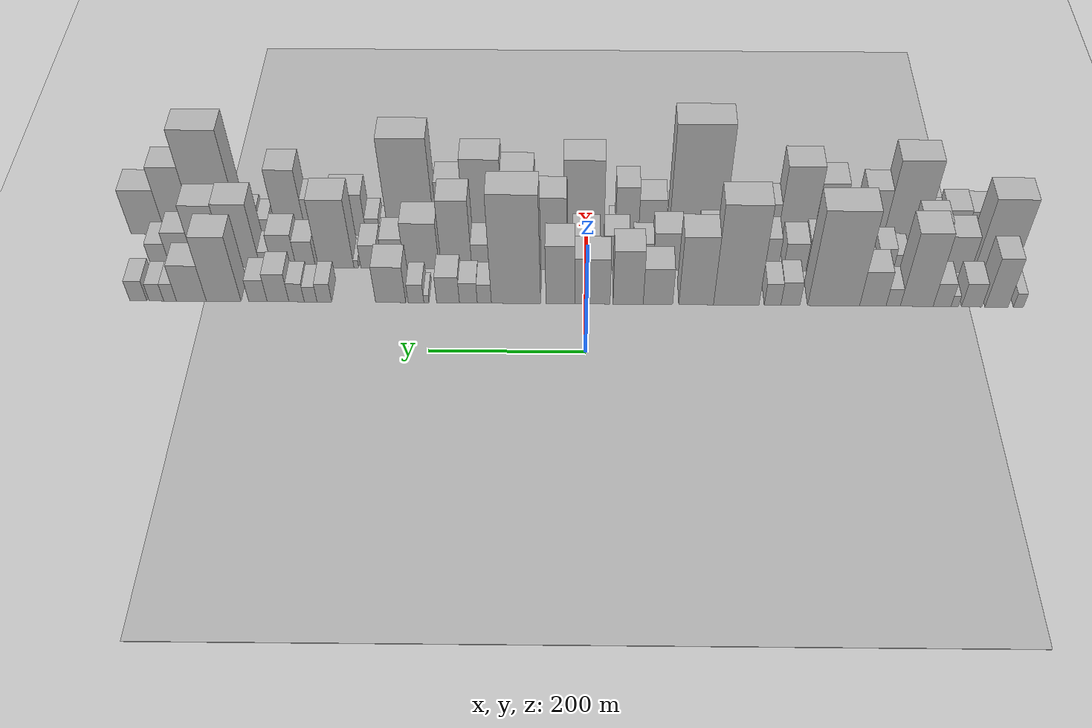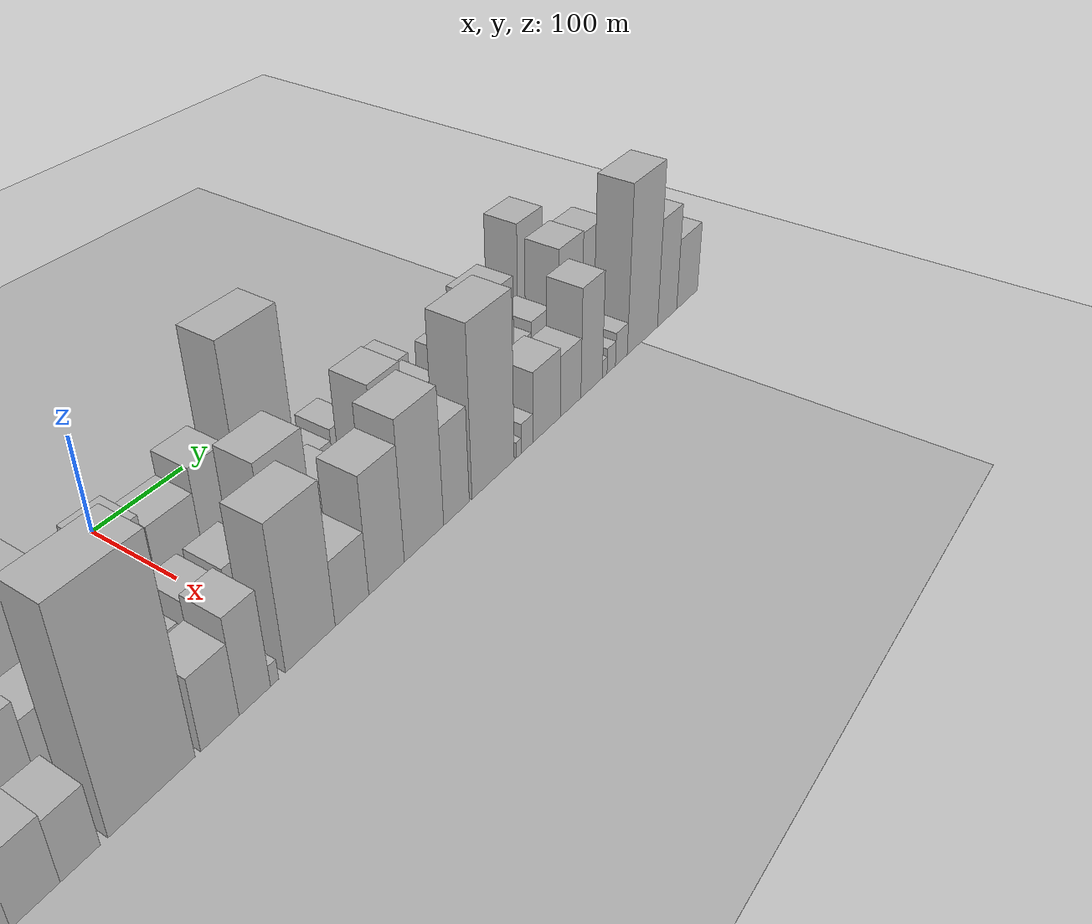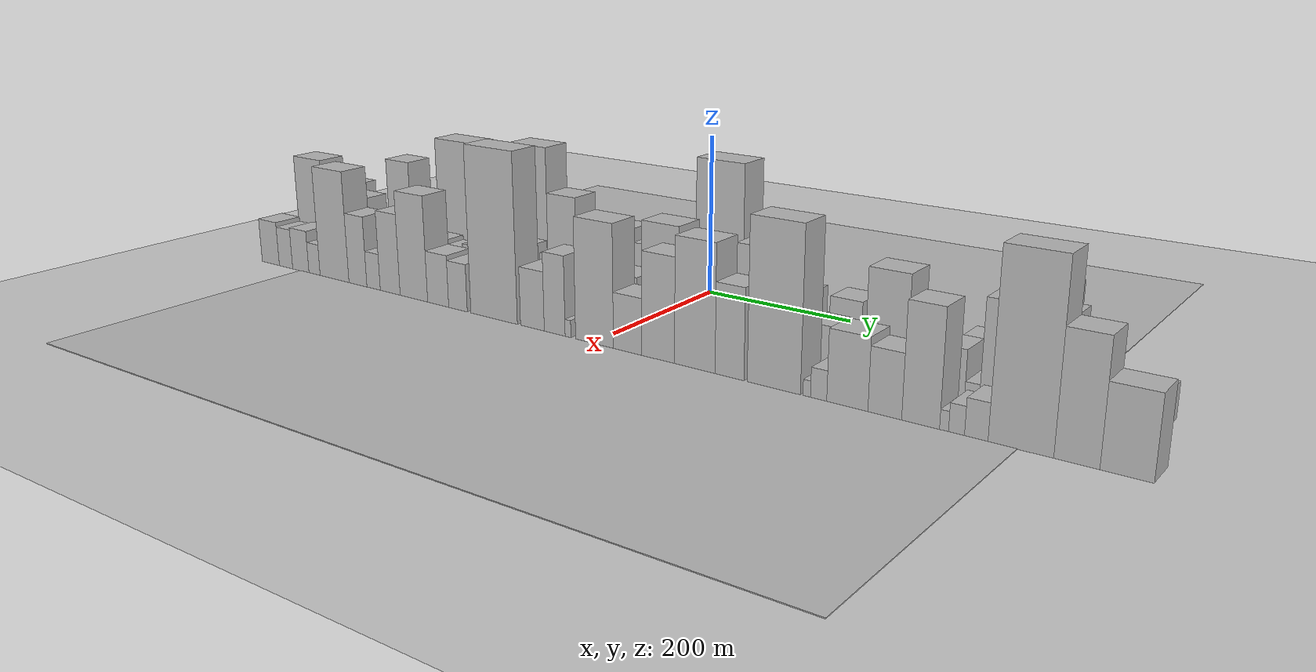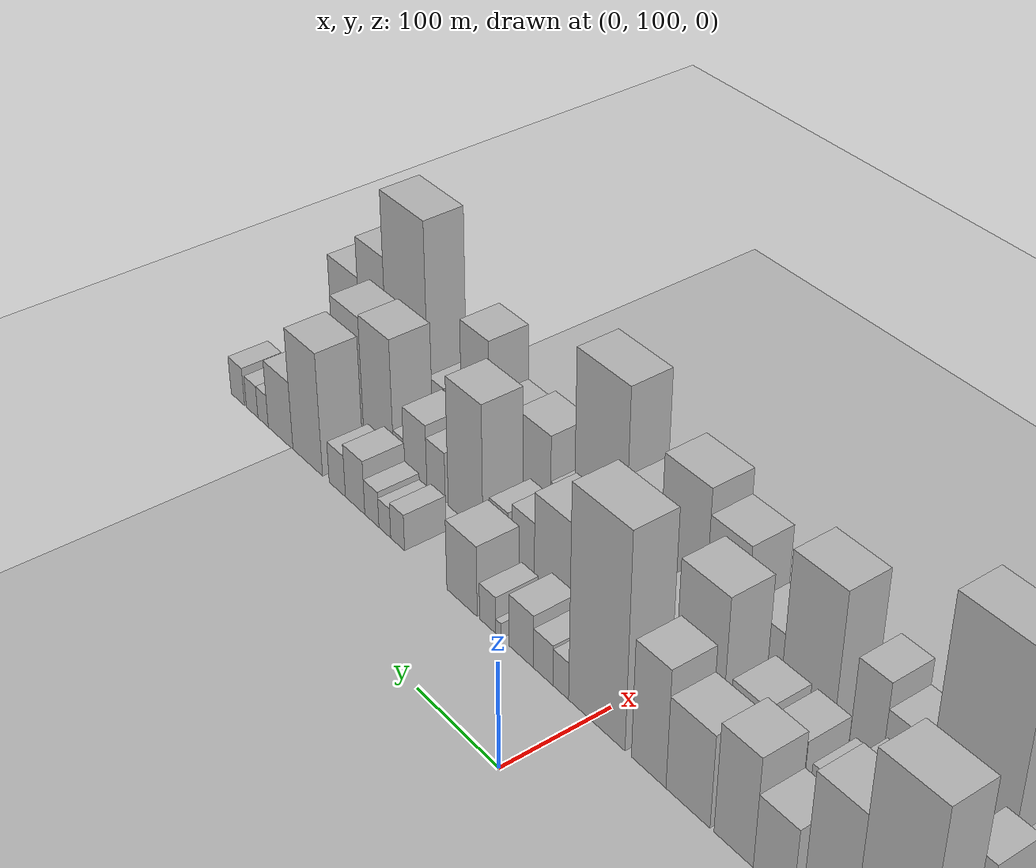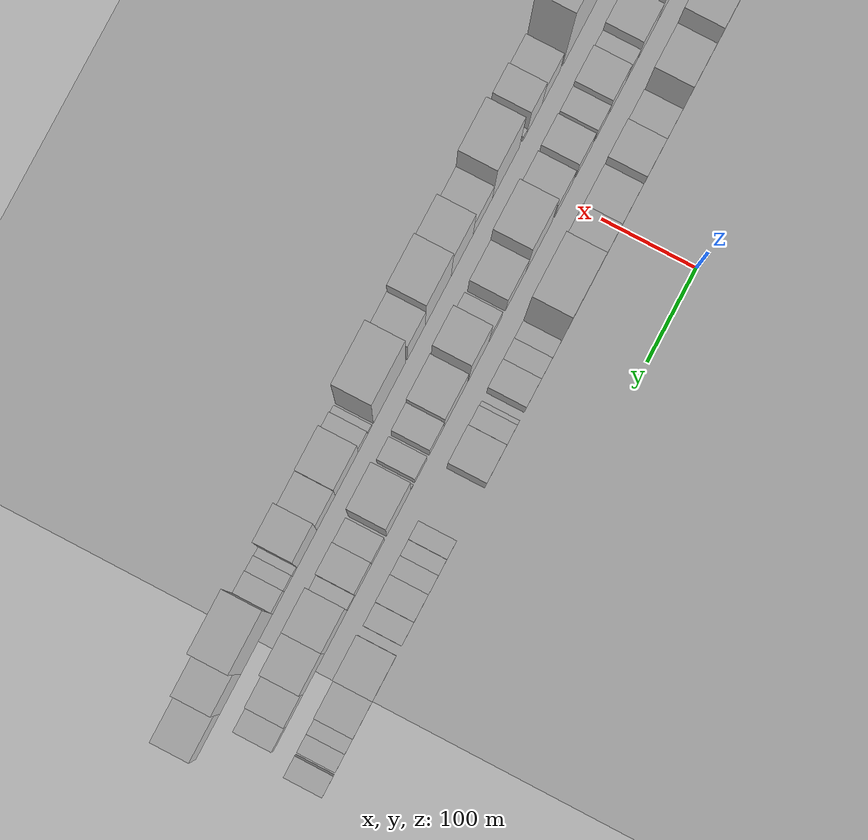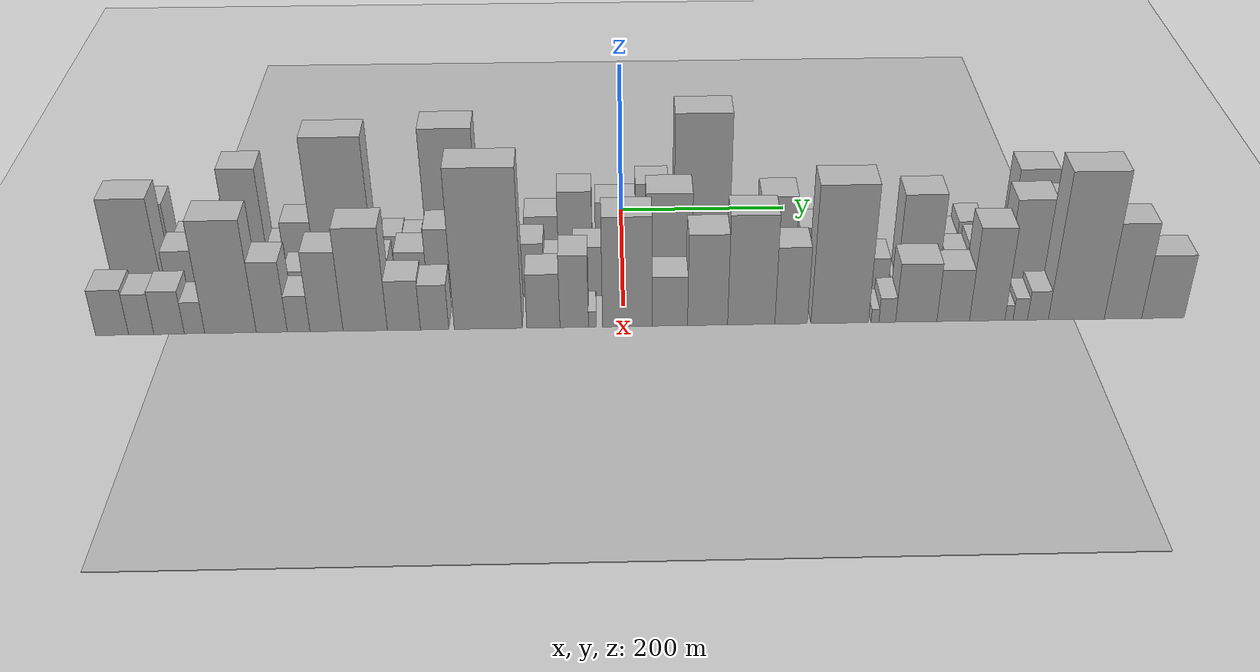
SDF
<?xml version="1.0" encoding="utf-8"?>

<sdf version="1.6">

   <world name="default">

      <gui fullscreen="0">

         <camera name="user_camera">

            <pose>-15 0 4.57585 0 0 0</pose>

            <view_controller>orbit</view_controller>

         </camera>

      </gui>

      <scene>

         <sky>

           <clouds>

             <speed>12</speed>

           </clouds>

         </sky>

         <ambient>0.4 0.4 0.4 1</ambient>

         <background>0.7 0.7 0.7 1</background>

         <shadows>1</shadows>

      </scene>

      <gravity>0 0 -9.8066</gravity>

      <magnetic_field>6e-06 2.3e-05 -4.2e-05</magnetic_field>

      <physics default="0" name="default_physics" type="ode">

         <ode>

            <solver>

               <type>quick</type>

               <iters>10</iters>

               <sor>1.0</sor>

               <use_dynamic_moi_rescaling>0</use_dynamic_moi_rescaling>

            </solver>

            <constraints>

               <cfm>0</cfm>

               <erp>0.2</erp>

               <contact_max_correcting_vel>100</contact_max_correcting_vel>

               <contact_surface_layer>0.001</contact_surface_layer>

            </constraints>

         </ode>

         <max_step_size>0.004</max_step_size>

         <real_time_factor>1</real_time_factor>

         <real_time_update_rate>250</real_time_update_rate>

      </physics>

      <light name="sun" type="directional">

         <cast_shadows>1</cast_shadows>

         <pose>0 0 10 0 0 0</pose>

         <diffuse>0.8 0.8 0.8 1</diffuse>

         <specular>0.2 0.2 0.2 1</specular>

         <attenuation>

            <range>1000</range>

            <constant>0.9</constant>

            <linear>0.01</linear>

            <quadratic>0.001</quadratic>

         </attenuation>

         <direction>-0.5 0.1 -0.9</direction>

      </light>

      <include>

         <name>ground_plane_1</name>

         <uri>model://HANNAS_ground_plane</uri>

         <pose>0 0 0  0 0 0</pose>

      </include>

      <include>

         <name>ground_plane_2</name>

         <uri>model://HANNAS_ground_plane</uri>

         <pose>100 0 0  0 0 0</pose>

      </include>

      <model name="building_1">

         <static>1</static>

         <pose frame="">100.0000 -564.4238 0 0.000000 0.000000 0.000000</pose>

         <link name="link">

            <pose frame="">0 0 13.50 0 0 0</pose>

            <collision name="collision">

               <geometry>

                  <box>

                     <size>40.0000 13.1523 27.0000</size>

                  </box>

               </geometry>

               <max_contacts>10</max_contacts>

               <surface>

                  <contact>

                     <ode/>

                  </contact>

                  <bounce/>

                  <friction>

                     <torsional>

                        <ode/>

                     </torsional>

                     <ode/>

                  </friction>

               </surface>

            </collision>

            <visual name="visual">

               <cast_shadows>0</cast_shadows>

               <geometry>

                  <box>

                     <size>40.0000 13.1523 27.0000</size>

                  </box>

               </geometry>

               <material>

                  <script>

                     <uri>model://HANNAS_wall/materials/scripts</uri>

                     <uri>model://HANNAS_wall/materials/textures</uri>

                     <name>vrc/HANNAS_wall</name>

                  </script>

               </material>

            </visual>

            <self_collide>0</self_collide>

            <enable_wind>0</enable_wind>

            <kinematic>0</kinematic>

         </link>

      </model>

      <model name="building_2">

         <static>1</static>

         <pose frame="">100.0000 -535.8039 0 0.000000 0.000000 0.000000</pose>

         <link name="link">

            <pose frame="">0 0 46.50 0 0 0</pose>

            <collision name="collision">

               <geometry>

                  <box>

                     <size>40.0000 30.0876 93.0000</size>

                  </box>

               </geometry>

               <max_contacts>10</max_contacts>

               <surface>

                  <contact>

                     <ode/>

                  </contact>

                  <bounce/>

                  <friction>

                     <torsional>

                        <ode/>

                     </torsional>

                     <ode/>

                  </friction>

               </surface>

            </collision>

            <visual name="visual">

               <cast_shadows>0</cast_shadows>

               <geometry>

                  <box>

                     <size>40.0000 30.0876 93.0000</size>

                  </box>

               </geometry>

               <material>

                  <script>

                     <uri>model://HANNAS_wall/materials/scripts</uri>

                     <uri>model://HANNAS_wall/materials/textures</uri>

                     <name>vrc/HANNAS_wall</name>

                  </script>

               </material>

            </visual>

            <self_collide>0</self_collide>

            <enable_wind>0</enable_wind>

            <kinematic>0</kinematic>

         </link>

      </model>

      <model name="building_3">

         <static>1</static>

         <pose frame="">100.0000 -503.4080 0 0.000000 0.000000 0.000000</pose>

         <link name="link">

            <pose frame="">0 0 22.50 0 0 0</pose>

            <collision name="collision">

               <geometry>

                  <box>

                     <size>40.0000 26.7042 45.0000</size>

                  </box>

               </geometry>

               <max_contacts>10</max_contacts>

               <surface>

                  <contact>

                     <ode/>

                  </contact>

                  <bounce/>

                  <friction>

                     <torsional>

                        <ode/>

                     </torsional>

                     <ode/>

                  </friction>

               </surface>

            </collision>

            <visual name="visual">

               <cast_shadows>0</cast_shadows>

               <geometry>

                  <box>

                     <size>40.0000 26.7042 45.0000</size>

                  </box>

               </geometry>

               <material>

                  <script>

                     <uri>model://HANNAS_wall/materials/scripts</uri>

                     <uri>model://HANNAS_wall/materials/textures</uri>

                     <name>vrc/HANNAS_wall</name>

                  </script>

               </material>

            </visual>

            <self_collide>0</self_collide>

            <enable_wind>0</enable_wind>

            <kinematic>0</kinematic>

         </link>

      </model>

      <model name="building_4">

         <static>1</static>

         <pose frame="">100.0000 -481.3256 0 0.000000 0.000000 0.000000</pose>

         <link name="link">

            <pose frame="">0 0 10.50 0 0 0</pose>

            <collision name="collision">

               <geometry>

                  <box>

                     <size>40.0000 9.4607 21.0000</size>

                  </box>

               </geometry>

               <max_contacts>10</max_contacts>

               <surface>

                  <contact>

                     <ode/>

                  </contact>

                  <bounce/>

                  <friction>

                     <torsional>

                        <ode/>

                     </torsional>

                     <ode/>

                  </friction>

               </surface>

            </collision>

            <visual name="visual">

               <cast_shadows>0</cast_shadows>

               <geometry>

                  <box>

                     <size>40.0000 9.4607 21.0000</size>

                  </box>

               </geometry>

               <material>

                  <script>

                     <uri>model://HANNAS_wall/materials/scripts</uri>

                     <uri>model://HANNAS_wall/materials/textures</uri>

                     <name>vrc/HANNAS_wall</name>

                  </script>

               </material>

            </visual>

            <self_collide>0</self_collide>

            <enable_wind>0</enable_wind>

            <kinematic>0</kinematic>

         </link>

      </model>

      <model name="building_5">

         <static>1</static>

         <pose frame="">100.0000 -464.8763 0 0.000000 0.000000 0.000000</pose>

         <link name="link">

            <pose frame="">0 0 22.50 0 0 0</pose>

            <collision name="collision">

               <geometry>

                  <box>

                     <size>40.0000 23.4379 45.0000</size>

                  </box>

               </geometry>

               <max_contacts>10</max_contacts>

               <surface>

                  <contact>

                     <ode/>

                  </contact>

                  <bounce/>

                  <friction>

                     <torsional>

                        <ode/>

                     </torsional>

                     <ode/>

                  </friction>

               </surface>

            </collision>

            <visual name="visual">

               <cast_shadows>0</cast_shadows>

               <geometry>

                  <box>

                     <size>40.0000 23.4379 45.0000</size>

                  </box>

               </geometry>

               <material>

                  <script>

                     <uri>model://HANNAS_wall/materials/scripts</uri>

                     <uri>model://HANNAS_wall/materials/textures</uri>

                     <name>vrc/HANNAS_wall</name>

                  </script>

               </material>

            </visual>

            <self_collide>0</self_collide>

            <enable_wind>0</enable_wind>

            <kinematic>0</kinematic>

         </link>

      </model>

      <model name="building_6">

         <static>1</static>

         <pose frame="">100.0000 -431.7220 0 0.000000 0.000000 0.000000</pose>

         <link name="link">

            <pose frame="">0 0 69.00 0 0 0</pose>

            <collision name="collision">

               <geometry>

                  <box>

                     <size>40.0000 42.8707 138.0000</size>

                  </box>

               </geometry>

               <max_contacts>10</max_contacts>

               <surface>

                  <contact>

                     <ode/>

                  </contact>

                  <bounce/>

                  <friction>

                     <torsional>

                        <ode/>

                     </torsional>

                     <ode/>

                  </friction>

               </surface>

            </collision>

            <visual name="visual">

               <cast_shadows>0</cast_shadows>

               <geometry>

                  <box>

                     <size>40.0000 42.8707 138.0000</size>

                  </box>

               </geometry>

               <material>

                  <script>

                     <uri>model://HANNAS_wall/materials/scripts</uri>

                     <uri>model://HANNAS_wall/materials/textures</uri>

                     <name>vrc/HANNAS_wall</name>

                  </script>

               </material>

            </visual>

            <self_collide>0</self_collide>

            <enable_wind>0</enable_wind>

            <kinematic>0</kinematic>

         </link>

      </model>

      <model name="building_7">

         <static>1</static>

         <pose frame="">100.0000 -400.9709 0 0.000000 0.000000 0.000000</pose>

         <link name="link">

            <pose frame="">0 0 16.50 0 0 0</pose>

            <collision name="collision">

               <geometry>

                  <box>

                     <size>40.0000 18.6314 33.0000</size>

                  </box>

               </geometry>

               <max_contacts>10</max_contacts>

               <surface>

                  <contact>

                     <ode/>

                  </contact>

                  <bounce/>

                  <friction>

                     <torsional>

                        <ode/>

                     </torsional>

                     <ode/>

                  </friction>

               </surface>

            </collision>

            <visual name="visual">

               <cast_shadows>0</cast_shadows>

               <geometry>

                  <box>

                     <size>40.0000 18.6314 33.0000</size>

                  </box>

               </geometry>

               <material>

                  <script>

                     <uri>model://HANNAS_wall/materials/scripts</uri>

                     <uri>model://HANNAS_wall/materials/textures</uri>

                     <name>vrc/HANNAS_wall</name>

                  </script>

               </material>

            </visual>

            <self_collide>0</self_collide>

            <enable_wind>0</enable_wind>

            <kinematic>0</kinematic>

         </link>

      </model>

      <model name="building_8">

         <static>1</static>

         <pose frame="">100.0000 -374.4194 0 0.000000 0.000000 0.000000</pose>

         <link name="link">

            <pose frame="">0 0 33.00 0 0 0</pose>

            <collision name="collision">

               <geometry>

                  <box>

                     <size>40.0000 34.4717 66.0000</size>

                  </box>

               </geometry>

               <max_contacts>10</max_contacts>

               <surface>

                  <contact>

                     <ode/>

                  </contact>

                  <bounce/>

                  <friction>

                     <torsional>

                        <ode/>

                     </torsional>

                     <ode/>

                  </friction>

               </surface>

            </collision>

            <visual name="visual">

               <cast_shadows>0</cast_shadows>

               <geometry>

                  <box>

                     <size>40.0000 34.4717 66.0000</size>

                  </box>

               </geometry>

               <material>

                  <script>

                     <uri>model://HANNAS_wall/materials/scripts</uri>

                     <uri>model://HANNAS_wall/materials/textures</uri>

                     <name>vrc/HANNAS_wall</name>

                  </script>

               </material>

            </visual>

            <self_collide>0</self_collide>

            <enable_wind>0</enable_wind>

            <kinematic>0</kinematic>

         </link>

      </model>

      <model name="building_9">

         <static>1</static>

         <pose frame="">100.0000 -323.2241 0 0.000000 0.000000 0.000000</pose>

         <link name="link">

            <pose frame="">0 0 88.50 0 0 0</pose>

            <collision name="collision">

               <geometry>

                  <box>

                     <size>40.0000 67.9188 177.0000</size>

                  </box>

               </geometry>

               <max_contacts>10</max_contacts>

               <surface>

                  <contact>

                     <ode/>

                  </contact>

                  <bounce/>

                  <friction>

                     <torsional>

                        <ode/>

                     </torsional>

                     <ode/>

                  </friction>

               </surface>

            </collision>

            <visual name="visual">

               <cast_shadows>0</cast_shadows>

               <geometry>

                  <box>

                     <size>40.0000 67.9188 177.0000</size>

                  </box>

               </geometry>

               <material>

                  <script>

                     <uri>model://HANNAS_wall/materials/scripts</uri>

                     <uri>model://HANNAS_wall/materials/textures</uri>

                     <name>vrc/HANNAS_wall</name>

                  </script>

               </material>

            </visual>

            <self_collide>0</self_collide>

            <enable_wind>0</enable_wind>

            <kinematic>0</kinematic>

         </link>

      </model>

      <model name="building_10">

         <static>1</static>

         <pose frame="">100.0000 -266.8234 0 0.000000 0.000000 0.000000</pose>

         <link name="link">

            <pose frame="">0 0 22.50 0 0 0</pose>

            <collision name="collision">

               <geometry>

                  <box>

                     <size>40.0000 24.8826 45.0000</size>

                  </box>

               </geometry>

               <max_contacts>10</max_contacts>

               <surface>

                  <contact>

                     <ode/>

                  </contact>

                  <bounce/>

                  <friction>

                     <torsional>

                        <ode/>

                     </torsional>

                     <ode/>

                  </friction>

               </surface>

            </collision>

            <visual name="visual">

               <cast_shadows>0</cast_shadows>

               <geometry>

                  <box>

                     <size>40.0000 24.8826 45.0000</size>

                  </box>

               </geometry>

               <material>

                  <script>

                     <uri>model://HANNAS_wall/materials/scripts</uri>

                     <uri>model://HANNAS_wall/materials/textures</uri>

                     <name>vrc/HANNAS_wall</name>

                  </script>

               </material>

            </visual>

            <self_collide>0</self_collide>

            <enable_wind>0</enable_wind>

            <kinematic>0</kinematic>

         </link>

      </model>

      <model name="building_11">

         <static>1</static>

         <pose frame="">100.0000 -243.5627 0 0.000000 0.000000 0.000000</pose>

         <link name="link">

            <pose frame="">0 0 21.00 0 0 0</pose>

            <collision name="collision">

               <geometry>

                  <box>

                     <size>40.0000 21.6390 42.0000</size>

                  </box>

               </geometry>

               <max_contacts>10</max_contacts>

               <surface>

                  <contact>

                     <ode/>

                  </contact>

                  <bounce/>

                  <friction>

                     <torsional>

                        <ode/>

                     </torsional>

                     <ode/>

                  </friction>

               </surface>

            </collision>

            <visual name="visual">

               <cast_shadows>0</cast_shadows>

               <geometry>

                  <box>

                     <size>40.0000 21.6390 42.0000</size>

                  </box>

               </geometry>

               <material>

                  <script>

                     <uri>model://HANNAS_wall/materials/scripts</uri>

                     <uri>model://HANNAS_wall/materials/textures</uri>

                     <name>vrc/HANNAS_wall</name>

                  </script>

               </material>

            </visual>

            <self_collide>0</self_collide>

            <enable_wind>0</enable_wind>

            <kinematic>0</kinematic>

         </link>

      </model>

      <model name="building_12">

         <static>1</static>

         <pose frame="">100.0000 -196.0559 0 0.000000 0.000000 0.000000</pose>

         <link name="link">

            <pose frame="">0 0 93.00 0 0 0</pose>

            <collision name="collision">

               <geometry>

                  <box>

                     <size>40.0000 59.3746 186.0000</size>

                  </box>

               </geometry>

               <max_contacts>10</max_contacts>

               <surface>

                  <contact>

                     <ode/>

                  </contact>

                  <bounce/>

                  <friction>

                     <torsional>

                        <ode/>

                     </torsional>

                     <ode/>

                  </friction>

               </surface>

            </collision>

            <visual name="visual">

               <cast_shadows>0</cast_shadows>

               <geometry>

                  <box>

                     <size>40.0000 59.3746 186.0000</size>

                  </box>

               </geometry>

               <material>

                  <script>

                     <uri>model://HANNAS_wall/materials/scripts</uri>

                     <uri>model://HANNAS_wall/materials/textures</uri>

                     <name>vrc/HANNAS_wall</name>

                  </script>

               </material>

            </visual>

            <self_collide>0</self_collide>

            <enable_wind>0</enable_wind>

            <kinematic>0</kinematic>

         </link>

      </model>

      <model name="building_13">

         <static>1</static>

         <pose frame="">100.0000 -143.6979 0 0.000000 0.000000 0.000000</pose>

         <link name="link">

            <pose frame="">0 0 64.50 0 0 0</pose>

            <collision name="collision">

               <geometry>

                  <box>

                     <size>40.0000 45.3413 129.0000</size>

                  </box>

               </geometry>

               <max_contacts>10</max_contacts>

               <surface>

                  <contact>

                     <ode/>

                  </contact>

                  <bounce/>

                  <friction>

                     <torsional>

                        <ode/>

                     </torsional>

                     <ode/>

                  </friction>

               </surface>

            </collision>

            <visual name="visual">

               <cast_shadows>0</cast_shadows>

               <geometry>

                  <box>

                     <size>40.0000 45.3413 129.0000</size>

                  </box>

               </geometry>

               <material>

                  <script>

                     <uri>model://HANNAS_wall/materials/scripts</uri>

                     <uri>model://HANNAS_wall/materials/textures</uri>

                     <name>vrc/HANNAS_wall</name>

                  </script>

               </material>

            </visual>

            <self_collide>0</self_collide>

            <enable_wind>0</enable_wind>

            <kinematic>0</kinematic>

         </link>

      </model>

      <model name="building_14">

         <static>1</static>

         <pose frame="">100.0000 -93.7879 0 0.000000 0.000000 0.000000</pose>

         <link name="link">

            <pose frame="">0 0 34.50 0 0 0</pose>

            <collision name="collision">

               <geometry>

                  <box>

                     <size>40.0000 38.4788 69.0000</size>

                  </box>

               </geometry>

               <max_contacts>10</max_contacts>

               <surface>

                  <contact>

                     <ode/>

                  </contact>

                  <bounce/>

                  <friction>

                     <torsional>

                        <ode/>

                     </torsional>

                     <ode/>

                  </friction>

               </surface>

            </collision>

            <visual name="visual">

               <cast_shadows>0</cast_shadows>

               <geometry>

                  <box>

                     <size>40.0000 38.4788 69.0000</size>

                  </box>

               </geometry>

               <material>

                  <script>

                     <uri>model://HANNAS_wall/materials/scripts</uri>

                     <uri>model://HANNAS_wall/materials/textures</uri>

                     <name>vrc/HANNAS_wall</name>

                  </script>

               </material>

            </visual>

            <self_collide>0</self_collide>

            <enable_wind>0</enable_wind>

            <kinematic>0</kinematic>

         </link>

      </model>

      <model name="building_15">

         <static>1</static>

         <pose frame="">100.0000 -54.8246 0 0.000000 0.000000 0.000000</pose>

         <link name="link">

            <pose frame="">0 0 51.00 0 0 0</pose>

            <collision name="collision">

               <geometry>

                  <box>

                     <size>40.0000 39.4477 102.0000</size>

                  </box>

               </geometry>

               <max_contacts>10</max_contacts>

               <surface>

                  <contact>

                     <ode/>

                  </contact>

                  <bounce/>

                  <friction>

                     <torsional>

                        <ode/>

                     </torsional>

                     <ode/>

                  </friction>

               </surface>

            </collision>

            <visual name="visual">

               <cast_shadows>0</cast_shadows>

               <geometry>

                  <box>

                     <size>40.0000 39.4477 102.0000</size>

                  </box>

               </geometry>

               <material>

                  <script>

                     <uri>model://HANNAS_wall/materials/scripts</uri>

                     <uri>model://HANNAS_wall/materials/textures</uri>

                     <name>vrc/HANNAS_wall</name>

                  </script>

               </material>

            </visual>

            <self_collide>0</self_collide>

            <enable_wind>0</enable_wind>

            <kinematic>0</kinematic>

         </link>

      </model>

      <model name="building_16">

         <static>1</static>

         <pose frame="">100.0000 -8.0166 0 0.000000 0.000000 0.000000</pose>

         <link name="link">

            <pose frame="">0 0 43.50 0 0 0</pose>

            <collision name="collision">

               <geometry>

                  <box>

                     <size>40.0000 46.1682 87.0000</size>

                  </box>

               </geometry>

               <max_contacts>10</max_contacts>

               <surface>

                  <contact>

                     <ode/>

                  </contact>

                  <bounce/>

                  <friction>

                     <torsional>

                        <ode/>

                     </torsional>

                     <ode/>

                  </friction>

               </surface>

            </collision>

            <visual name="visual">

               <cast_shadows>0</cast_shadows>

               <geometry>

                  <box>

                     <size>40.0000 46.1682 87.0000</size>

                  </box>

               </geometry>

               <material>

                  <script>

                     <uri>model://HANNAS_wall/materials/scripts</uri>

                     <uri>model://HANNAS_wall/materials/textures</uri>

                     <name>vrc/HANNAS_wall</name>

                  </script>

               </material>

            </visual>

            <self_collide>0</self_collide>

            <enable_wind>0</enable_wind>

            <kinematic>0</kinematic>

         </link>

      </model>

      <model name="building_17">

         <static>1</static>

         <pose frame="">100.0000 33.8189 0 0.000000 0.000000 0.000000</pose>

         <link name="link">

            <pose frame="">0 0 55.50 0 0 0</pose>

            <collision name="collision">

               <geometry>

                  <box>

                     <size>40.0000 37.5027 111.0000</size>

                  </box>

               </geometry>

               <max_contacts>10</max_contacts>

               <surface>

                  <contact>

                     <ode/>

                  </contact>

                  <bounce/>

                  <friction>

                     <torsional>

                        <ode/>

                     </torsional>

                     <ode/>

                  </friction>

               </surface>

            </collision>

            <visual name="visual">

               <cast_shadows>0</cast_shadows>

               <geometry>

                  <box>

                     <size>40.0000 37.5027 111.0000</size>

                  </box>

               </geometry>

               <material>

                  <script>

                     <uri>model://HANNAS_wall/materials/scripts</uri>

                     <uri>model://HANNAS_wall/materials/textures</uri>

                     <name>vrc/HANNAS_wall</name>

                  </script>

               </material>

            </visual>

            <self_collide>0</self_collide>

            <enable_wind>0</enable_wind>

            <kinematic>0</kinematic>

         </link>

      </model>

      <model name="building_18">

         <static>1</static>

         <pose frame="">100.0000 91.8025 0 0.000000 0.000000 0.000000</pose>

         <link name="link">

            <pose frame="">0 0 100.50 0 0 0</pose>

            <collision name="collision">

               <geometry>

                  <box>

                     <size>40.0000 64.4647 201.0000</size>

                  </box>

               </geometry>

               <max_contacts>10</max_contacts>

               <surface>

                  <contact>

                     <ode/>

                  </contact>

                  <bounce/>

                  <friction>

                     <torsional>

                        <ode/>

                     </torsional>

                     <ode/>

                  </friction>

               </surface>

            </collision>

            <visual name="visual">

               <cast_shadows>0</cast_shadows>

               <geometry>

                  <box>

                     <size>40.0000 64.4647 201.0000</size>

                  </box>

               </geometry>

               <material>

                  <script>

                     <uri>model://HANNAS_wall/materials/scripts</uri>

                     <uri>model://HANNAS_wall/materials/textures</uri>

                     <name>vrc/HANNAS_wall</name>

                  </script>

               </material>

            </visual>

            <self_collide>0</self_collide>

            <enable_wind>0</enable_wind>

            <kinematic>0</kinematic>

         </link>

      </model>

      <model name="building_19">

         <static>1</static>

         <pose frame="">100.0000 133.2769 0 0.000000 0.000000 0.000000</pose>

         <link name="link">

            <pose frame="">0 0 18.00 0 0 0</pose>

            <collision name="collision">

               <geometry>

                  <box>

                     <size>40.0000 18.4841 36.0000</size>

                  </box>

               </geometry>

               <max_contacts>10</max_contacts>

               <surface>

                  <contact>

                     <ode/>

                  </contact>

                  <bounce/>

                  <friction>

                     <torsional>

                        <ode/>

                     </torsional>

                     <ode/>

                  </friction>

               </surface>

            </collision>

            <visual name="visual">

               <cast_shadows>0</cast_shadows>

               <geometry>

                  <box>

                     <size>40.0000 18.4841 36.0000</size>

                  </box>

               </geometry>

               <material>

                  <script>

                     <uri>model://HANNAS_wall/materials/scripts</uri>

                     <uri>model://HANNAS_wall/materials/textures</uri>

                     <name>vrc/HANNAS_wall</name>

                  </script>

               </material>

            </visual>

            <self_collide>0</self_collide>

            <enable_wind>0</enable_wind>

            <kinematic>0</kinematic>

         </link>

      </model>

      <model name="building_20">

         <static>1</static>

         <pose frame="">100.0000 154.1887 0 0.000000 0.000000 0.000000</pose>

         <link name="link">

            <pose frame="">0 0 19.50 0 0 0</pose>

            <collision name="collision">

               <geometry>

                  <box>

                     <size>40.0000 23.3394 39.0000</size>

                  </box>

               </geometry>

               <max_contacts>10</max_contacts>

               <surface>

                  <contact>

                     <ode/>

                  </contact>

                  <bounce/>

                  <friction>

                     <torsional>

                        <ode/>

                     </torsional>

                     <ode/>

                  </friction>

               </surface>

            </collision>

            <visual name="visual">

               <cast_shadows>0</cast_shadows>

               <geometry>

                  <box>

                     <size>40.0000 23.3394 39.0000</size>

                  </box>

               </geometry>

               <material>

                  <script>

                     <uri>model://HANNAS_wall/materials/scripts</uri>

                     <uri>model://HANNAS_wall/materials/textures</uri>

                     <name>vrc/HANNAS_wall</name>

                  </script>

               </material>

            </visual>

            <self_collide>0</self_collide>

            <enable_wind>0</enable_wind>

            <kinematic>0</kinematic>

         </link>

      </model>

      <model name="building_21">

         <static>1</static>

         <pose frame="">100.0000 180.8132 0 0.000000 0.000000 0.000000</pose>

         <link name="link">

            <pose frame="">0 0 25.50 0 0 0</pose>

            <collision name="collision">

               <geometry>

                  <box>

                     <size>40.0000 29.9097 51.0000</size>

                  </box>

               </geometry>

               <max_contacts>10</max_contacts>

               <surface>

                  <contact>

                     <ode/>

                  </contact>

                  <bounce/>

                  <friction>

                     <torsional>

                        <ode/>

                     </torsional>

                     <ode/>

                  </friction>

               </surface>

            </collision>

            <visual name="visual">

               <cast_shadows>0</cast_shadows>

               <geometry>

                  <box>

                     <size>40.0000 29.9097 51.0000</size>

                  </box>

               </geometry>

               <material>

                  <script>

                     <uri>model://HANNAS_wall/materials/scripts</uri>

                     <uri>model://HANNAS_wall/materials/textures</uri>

                     <name>vrc/HANNAS_wall</name>

                  </script>

               </material>

            </visual>

            <self_collide>0</self_collide>

            <enable_wind>0</enable_wind>

            <kinematic>0</kinematic>

         </link>

      </model>

      <model name="building_22">

         <static>1</static>

         <pose frame="">100.0000 209.1405 0 0.000000 0.000000 0.000000</pose>

         <link name="link">

            <pose frame="">0 0 7.50 0 0 0</pose>

            <collision name="collision">

               <geometry>

                  <box>

                     <size>40.0000 6.7450 15.0000</size>

                  </box>

               </geometry>

               <max_contacts>10</max_contacts>

               <surface>

                  <contact>

                     <ode/>

                  </contact>

                  <bounce/>

                  <friction>

                     <torsional>

                        <ode/>

                     </torsional>

                     <ode/>

                  </friction>

               </surface>

            </collision>

            <visual name="visual">

               <cast_shadows>0</cast_shadows>

               <geometry>

                  <box>

                     <size>40.0000 6.7450 15.0000</size>

                  </box>

               </geometry>

               <material>

                  <script>

                     <uri>model://HANNAS_wall/materials/scripts</uri>

                     <uri>model://HANNAS_wall/materials/textures</uri>

                     <name>vrc/HANNAS_wall</name>

                  </script>

               </material>

            </visual>

            <self_collide>0</self_collide>

            <enable_wind>0</enable_wind>

            <kinematic>0</kinematic>

         </link>

      </model>

      <model name="building_23">

         <static>1</static>

         <pose frame="">100.0000 222.8368 0 0.000000 0.000000 0.000000</pose>

         <link name="link">

            <pose frame="">0 0 18.00 0 0 0</pose>

            <collision name="collision">

               <geometry>

                  <box>

                     <size>40.0000 20.6476 36.0000</size>

                  </box>

               </geometry>

               <max_contacts>10</max_contacts>

               <surface>

                  <contact>

                     <ode/>

                  </contact>

                  <bounce/>

                  <friction>

                     <torsional>

                        <ode/>

                     </torsional>

                     <ode/>

                  </friction>

               </surface>

            </collision>

            <visual name="visual">

               <cast_shadows>0</cast_shadows>

               <geometry>

                  <box>

                     <size>40.0000 20.6476 36.0000</size>

                  </box>

               </geometry>

               <material>

                  <script>

                     <uri>model://HANNAS_wall/materials/scripts</uri>

                     <uri>model://HANNAS_wall/materials/textures</uri>

                     <name>vrc/HANNAS_wall</name>

                  </script>

               </material>

            </visual>

            <self_collide>0</self_collide>

            <enable_wind>0</enable_wind>

            <kinematic>0</kinematic>

         </link>

      </model>

      <model name="building_24">

         <static>1</static>

         <pose frame="">100.0000 255.9552 0 0.000000 0.000000 0.000000</pose>

         <link name="link">

            <pose frame="">0 0 34.50 0 0 0</pose>

            <collision name="collision">

               <geometry>

                  <box>

                     <size>40.0000 39.5892 69.0000</size>

                  </box>

               </geometry>

               <max_contacts>10</max_contacts>

               <surface>

                  <contact>

                     <ode/>

                  </contact>

                  <bounce/>

                  <friction>

                     <torsional>

                        <ode/>

                     </torsional>

                     <ode/>

                  </friction>

               </surface>

            </collision>

            <visual name="visual">

               <cast_shadows>0</cast_shadows>

               <geometry>

                  <box>

                     <size>40.0000 39.5892 69.0000</size>

                  </box>

               </geometry>

               <material>

                  <script>

                     <uri>model://HANNAS_wall/materials/scripts</uri>

                     <uri>model://HANNAS_wall/materials/textures</uri>

                     <name>vrc/HANNAS_wall</name>

                  </script>

               </material>

            </visual>

            <self_collide>0</self_collide>

            <enable_wind>0</enable_wind>

            <kinematic>0</kinematic>

         </link>

      </model>

      <model name="building_25">

         <static>1</static>

         <pose frame="">100.0000 342.8090 0 0.000000 0.000000 0.000000</pose>

         <link name="link">

            <pose frame="">0 0 18.00 0 0 0</pose>

            <collision name="collision">

               <geometry>

                  <box>

                     <size>40.0000 19.3728 36.0000</size>

                  </box>

               </geometry>

               <max_contacts>10</max_contacts>

               <surface>

                  <contact>

                     <ode/>

                  </contact>

                  <bounce/>

                  <friction>

                     <torsional>

                        <ode/>

                     </torsional>

                     <ode/>

                  </friction>

               </surface>

            </collision>

            <visual name="visual">

               <cast_shadows>0</cast_shadows>

               <geometry>

                  <box>

                     <size>40.0000 19.3728 36.0000</size>

                  </box>

               </geometry>

               <material>

                  <script>

                     <uri>model://HANNAS_wall/materials/scripts</uri>

                     <uri>model://HANNAS_wall/materials/textures</uri>

                     <name>vrc/HANNAS_wall</name>

                  </script>

               </material>

            </visual>

            <self_collide>0</self_collide>

            <enable_wind>0</enable_wind>

            <kinematic>0</kinematic>

         </link>

      </model>

      <model name="building_26">

         <static>1</static>

         <pose frame="">100.0000 360.8640 0 0.000000 0.000000 0.000000</pose>

         <link name="link">

            <pose frame="">0 0 15.00 0 0 0</pose>

            <collision name="collision">

               <geometry>

                  <box>

                     <size>40.0000 16.7372 30.0000</size>

                  </box>

               </geometry>

               <max_contacts>10</max_contacts>

               <surface>

                  <contact>

                     <ode/>

                  </contact>

                  <bounce/>

                  <friction>

                     <torsional>

                        <ode/>

                     </torsional>

                     <ode/>

                  </friction>

               </surface>

            </collision>

            <visual name="visual">

               <cast_shadows>0</cast_shadows>

               <geometry>

                  <box>

                     <size>40.0000 16.7372 30.0000</size>

                  </box>

               </geometry>

               <material>

                  <script>

                     <uri>model://HANNAS_wall/materials/scripts</uri>

                     <uri>model://HANNAS_wall/materials/textures</uri>

                     <name>vrc/HANNAS_wall</name>

                  </script>

               </material>

            </visual>

            <self_collide>0</self_collide>

            <enable_wind>0</enable_wind>

            <kinematic>0</kinematic>

         </link>

      </model>

      <model name="building_27">

         <static>1</static>

         <pose frame="">100.0000 379.3544 0 0.000000 0.000000 0.000000</pose>

         <link name="link">

            <pose frame="">0 0 18.00 0 0 0</pose>

            <collision name="collision">

               <geometry>

                  <box>

                     <size>40.0000 20.2437 36.0000</size>

                  </box>

               </geometry>

               <max_contacts>10</max_contacts>

               <surface>

                  <contact>

                     <ode/>

                  </contact>

                  <bounce/>

                  <friction>

                     <torsional>

                        <ode/>

                     </torsional>

                     <ode/>

                  </friction>

               </surface>

            </collision>

            <visual name="visual">

               <cast_shadows>0</cast_shadows>

               <geometry>

                  <box>

                     <size>40.0000 20.2437 36.0000</size>

                  </box>

               </geometry>

               <material>

                  <script>

                     <uri>model://HANNAS_wall/materials/scripts</uri>

                     <uri>model://HANNAS_wall/materials/textures</uri>

                     <name>vrc/HANNAS_wall</name>

                  </script>

               </material>

            </visual>

            <self_collide>0</self_collide>

            <enable_wind>0</enable_wind>

            <kinematic>0</kinematic>

         </link>

      </model>

      <model name="building_28">

         <static>1</static>

         <pose frame="">100.0000 403.6639 0 0.000000 0.000000 0.000000</pose>

         <link name="link">

            <pose frame="">0 0 27.00 0 0 0</pose>

            <collision name="collision">

               <geometry>

                  <box>

                     <size>40.0000 28.3753 54.0000</size>

                  </box>

               </geometry>

               <max_contacts>10</max_contacts>

               <surface>

                  <contact>

                     <ode/>

                  </contact>

                  <bounce/>

                  <friction>

                     <torsional>

                        <ode/>

                     </torsional>

                     <ode/>

                  </friction>

               </surface>

            </collision>

            <visual name="visual">

               <cast_shadows>0</cast_shadows>

               <geometry>

                  <box>

                     <size>40.0000 28.3753 54.0000</size>

                  </box>

               </geometry>

               <material>

                  <script>

                     <uri>model://HANNAS_wall/materials/scripts</uri>

                     <uri>model://HANNAS_wall/materials/textures</uri>

                     <name>vrc/HANNAS_wall</name>

                  </script>

               </material>

            </visual>

            <self_collide>0</self_collide>

            <enable_wind>0</enable_wind>

            <kinematic>0</kinematic>

         </link>

      </model>

      <model name="building_29">

         <static>1</static>

         <pose frame="">100.0000 429.9659 0 0.000000 0.000000 0.000000</pose>

         <link name="link">

            <pose frame="">0 0 21.00 0 0 0</pose>

            <collision name="collision">

               <geometry>

                  <box>

                     <size>40.0000 24.2287 42.0000</size>

                  </box>

               </geometry>

               <max_contacts>10</max_contacts>

               <surface>

                  <contact>

                     <ode/>

                  </contact>

                  <bounce/>

                  <friction>

                     <torsional>

                        <ode/>

                     </torsional>

                     <ode/>

                  </friction>

               </surface>

            </collision>

            <visual name="visual">

               <cast_shadows>0</cast_shadows>

               <geometry>

                  <box>

                     <size>40.0000 24.2287 42.0000</size>

                  </box>

               </geometry>

               <material>

                  <script>

                     <uri>model://HANNAS_wall/materials/scripts</uri>

                     <uri>model://HANNAS_wall/materials/textures</uri>

                     <name>vrc/HANNAS_wall</name>

                  </script>

               </material>

            </visual>

            <self_collide>0</self_collide>

            <enable_wind>0</enable_wind>

            <kinematic>0</kinematic>

         </link>

      </model>

      <model name="building_30">

         <static>1</static>

         <pose frame="">100.0000 474.9152 0 0.000000 0.000000 0.000000</pose>

         <link name="link">

            <pose frame="">0 0 61.50 0 0 0</pose>

            <collision name="collision">

               <geometry>

                  <box>

                     <size>40.0000 45.6700 123.0000</size>

                  </box>

               </geometry>

               <max_contacts>10</max_contacts>

               <surface>

                  <contact>

                     <ode/>

                  </contact>

                  <bounce/>

                  <friction>

                     <torsional>

                        <ode/>

                     </torsional>

                     <ode/>

                  </friction>

               </surface>

            </collision>

            <visual name="visual">

               <cast_shadows>0</cast_shadows>

               <geometry>

                  <box>

                     <size>40.0000 45.6700 123.0000</size>

                  </box>

               </geometry>

               <material>

                  <script>

                     <uri>model://HANNAS_wall/materials/scripts</uri>

                     <uri>model://HANNAS_wall/materials/textures</uri>

                     <name>vrc/HANNAS_wall</name>

                  </script>

               </material>

            </visual>

            <self_collide>0</self_collide>

            <enable_wind>0</enable_wind>

            <kinematic>0</kinematic>

         </link>

      </model>

      <model name="building_31">

         <static>1</static>

         <pose frame="">100.0000 517.3630 0 0.000000 0.000000 0.000000</pose>

         <link name="link">

            <pose frame="">0 0 34.50 0 0 0</pose>

            <collision name="collision">

               <geometry>

                  <box>

                     <size>40.0000 39.2256 69.0000</size>

                  </box>

               </geometry>

               <max_contacts>10</max_contacts>

               <surface>

                  <contact>

                     <ode/>

                  </contact>

                  <bounce/>

                  <friction>

                     <torsional>

                        <ode/>

                     </torsional>

                     <ode/>

                  </friction>

               </surface>

            </collision>

            <visual name="visual">

               <cast_shadows>0</cast_shadows>

               <geometry>

                  <box>

                     <size>40.0000 39.2256 69.0000</size>

                  </box>

               </geometry>

               <material>

                  <script>

                     <uri>model://HANNAS_wall/materials/scripts</uri>

                     <uri>model://HANNAS_wall/materials/textures</uri>

                     <name>vrc/HANNAS_wall</name>

                  </script>

               </material>

            </visual>

            <self_collide>0</self_collide>

            <enable_wind>0</enable_wind>

            <kinematic>0</kinematic>

         </link>

      </model>

      <model name="building_32">

         <static>1</static>

         <pose frame="">100.0000 545.3870 0 0.000000 0.000000 0.000000</pose>

         <link name="link">

            <pose frame="">0 0 16.50 0 0 0</pose>

            <collision name="collision">

               <geometry>

                  <box>

                     <size>40.0000 16.8225 33.0000</size>

                  </box>

               </geometry>

               <max_contacts>10</max_contacts>

               <surface>

                  <contact>

                     <ode/>

                  </contact>

                  <bounce/>

                  <friction>

                     <torsional>

                        <ode/>

                     </torsional>

                     <ode/>

                  </friction>

               </surface>

            </collision>

            <visual name="visual">

               <cast_shadows>0</cast_shadows>

               <geometry>

                  <box>

                     <size>40.0000 16.8225 33.0000</size>

                  </box>

               </geometry>

               <material>

                  <script>

                     <uri>model://HANNAS_wall/materials/scripts</uri>

                     <uri>model://HANNAS_wall/materials/textures</uri>

                     <name>vrc/HANNAS_wall</name>

                  </script>

               </material>

            </visual>

            <self_collide>0</self_collide>

            <enable_wind>0</enable_wind>

            <kinematic>0</kinematic>

         </link>

      </model>

      <model name="building_33">

         <static>1</static>

         <pose frame="">100.0000 563.3105 0 0.000000 0.000000 0.000000</pose>

         <link name="link">

            <pose frame="">0 0 16.50 0 0 0</pose>

            <collision name="collision">

               <geometry>

                  <box>

                     <size>40.0000 19.0244 33.0000</size>

                  </box>

               </geometry>

               <max_contacts>10</max_contacts>

               <surface>

                  <contact>

                     <ode/>

                  </contact>

                  <bounce/>

                  <friction>

                     <torsional>

                        <ode/>

                     </torsional>

                     <ode/>

                  </friction>

               </surface>

            </collision>

            <visual name="visual">

               <cast_shadows>0</cast_shadows>

               <geometry>

                  <box>

                     <size>40.0000 19.0244 33.0000</size>

                  </box>

               </geometry>

               <material>

                  <script>

                     <uri>model://HANNAS_wall/materials/scripts</uri>

                     <uri>model://HANNAS_wall/materials/textures</uri>

                     <name>vrc/HANNAS_wall</name>

                  </script>

               </material>

            </visual>

            <self_collide>0</self_collide>

            <enable_wind>0</enable_wind>

            <kinematic>0</kinematic>

         </link>

      </model>

      <model name="building_34">

         <static>1</static>

         <pose frame="">100.0000 586.9795 0 0.000000 0.000000 0.000000</pose>

         <link name="link">

            <pose frame="">0 0 19.50 0 0 0</pose>

            <collision name="collision">

               <geometry>

                  <box>

                     <size>40.0000 22.3135 39.0000</size>

                  </box>

               </geometry>

               <max_contacts>10</max_contacts>

               <surface>

                  <contact>

                     <ode/>

                  </contact>

                  <bounce/>

                  <friction>

                     <torsional>

                        <ode/>

                     </torsional>

                     <ode/>

                  </friction>

               </surface>

            </collision>

            <visual name="visual">

               <cast_shadows>0</cast_shadows>

               <geometry>

                  <box>

                     <size>40.0000 22.3135 39.0000</size>

                  </box>

               </geometry>

               <material>

                  <script>

                     <uri>model://HANNAS_wall/materials/scripts</uri>

                     <uri>model://HANNAS_wall/materials/textures</uri>

                     <name>vrc/HANNAS_wall</name>

                  </script>

               </material>

            </visual>

            <self_collide>0</self_collide>

            <enable_wind>0</enable_wind>

            <kinematic>0</kinematic>

         </link>

      </model>

      <model name="building_35">

         <static>1</static>

         <pose frame="">160.0000 -544.0280 0 0.000000 0.000000 0.000000</pose>

         <link name="link">

            <pose frame="">0 0 69.00 0 0 0</pose>

            <collision name="collision">

               <geometry>

                  <box>

                     <size>40.0000 53.9440 138.0000</size>

                  </box>

               </geometry>

               <max_contacts>10</max_contacts>

               <surface>

                  <contact>

                     <ode/>

                  </contact>

                  <bounce/>

                  <friction>

                     <torsional>

                        <ode/>

                     </torsional>

                     <ode/>

                  </friction>

               </surface>

            </collision>

            <visual name="visual">

               <cast_shadows>0</cast_shadows>

               <geometry>

                  <box>

                     <size>40.0000 53.9440 138.0000</size>

                  </box>

               </geometry>

               <material>

                  <script>

                     <uri>model://HANNAS_wall/materials/scripts</uri>

                     <uri>model://HANNAS_wall/materials/textures</uri>

                     <name>vrc/HANNAS_wall</name>

                  </script>

               </material>

            </visual>

            <self_collide>0</self_collide>

            <enable_wind>0</enable_wind>

            <kinematic>0</kinematic>

         </link>

      </model>

      <model name="building_36">

         <static>1</static>

         <pose frame="">160.0000 -492.4621 0 0.000000 0.000000 0.000000</pose>

         <link name="link">

            <pose frame="">0 0 34.50 0 0 0</pose>

            <collision name="collision">

               <geometry>

                  <box>

                     <size>40.0000 41.1879 69.0000</size>

                  </box>

               </geometry>

               <max_contacts>10</max_contacts>

               <surface>

                  <contact>

                     <ode/>

                  </contact>

                  <bounce/>

                  <friction>

                     <torsional>

                        <ode/>

                     </torsional>

                     <ode/>

                  </friction>

               </surface>

            </collision>

            <visual name="visual">

               <cast_shadows>0</cast_shadows>

               <geometry>

                  <box>

                     <size>40.0000 41.1879 69.0000</size>

                  </box>

               </geometry>

               <material>

                  <script>

                     <uri>model://HANNAS_wall/materials/scripts</uri>

                     <uri>model://HANNAS_wall/materials/textures</uri>

                     <name>vrc/HANNAS_wall</name>

                  </script>

               </material>

            </visual>

            <self_collide>0</self_collide>

            <enable_wind>0</enable_wind>

            <kinematic>0</kinematic>

         </link>

      </model>

      <model name="building_37">

         <static>1</static>

         <pose frame="">160.0000 -453.2706 0 0.000000 0.000000 0.000000</pose>

         <link name="link">

            <pose frame="">0 0 48.00 0 0 0</pose>

            <collision name="collision">

               <geometry>

                  <box>

                     <size>40.0000 37.1951 96.0000</size>

                  </box>

               </geometry>

               <max_contacts>10</max_contacts>

               <surface>

                  <contact>

                     <ode/>

                  </contact>

                  <bounce/>

                  <friction>

                     <torsional>

                        <ode/>

                     </torsional>

                     <ode/>

                  </friction>

               </surface>

            </collision>

            <visual name="visual">

               <cast_shadows>0</cast_shadows>

               <geometry>

                  <box>

                     <size>40.0000 37.1951 96.0000</size>

                  </box>

               </geometry>

               <material>

                  <script>

                     <uri>model://HANNAS_wall/materials/scripts</uri>

                     <uri>model://HANNAS_wall/materials/textures</uri>

                     <name>vrc/HANNAS_wall</name>

                  </script>

               </material>

            </visual>

            <self_collide>0</self_collide>

            <enable_wind>0</enable_wind>

            <kinematic>0</kinematic>

         </link>

      </model>

      <model name="building_38">

         <static>1</static>

         <pose frame="">160.0000 -417.9296 0 0.000000 0.000000 0.000000</pose>

         <link name="link">

            <pose frame="">0 0 16.50 0 0 0</pose>

            <collision name="collision">

               <geometry>

                  <box>

                     <size>40.0000 17.4869 33.0000</size>

                  </box>

               </geometry>

               <max_contacts>10</max_contacts>

               <surface>

                  <contact>

                     <ode/>

                  </contact>

                  <bounce/>

                  <friction>

                     <torsional>

                        <ode/>

                     </torsional>

                     <ode/>

                  </friction>

               </surface>

            </collision>

            <visual name="visual">

               <cast_shadows>0</cast_shadows>

               <geometry>

                  <box>

                     <size>40.0000 17.4869 33.0000</size>

                  </box>

               </geometry>

               <material>

                  <script>

                     <uri>model://HANNAS_wall/materials/scripts</uri>

                     <uri>model://HANNAS_wall/materials/textures</uri>

                     <name>vrc/HANNAS_wall</name>

                  </script>

               </material>

            </visual>

            <self_collide>0</self_collide>

            <enable_wind>0</enable_wind>

            <kinematic>0</kinematic>

         </link>

      </model>

      <model name="building_39">

         <static>1</static>

         <pose frame="">160.0000 -397.1878 0 0.000000 0.000000 0.000000</pose>

         <link name="link">

            <pose frame="">0 0 22.50 0 0 0</pose>

            <collision name="collision">

               <geometry>

                  <box>

                     <size>40.0000 23.9967 45.0000</size>

                  </box>

               </geometry>

               <max_contacts>10</max_contacts>

               <surface>

                  <contact>

                     <ode/>

                  </contact>

                  <bounce/>

                  <friction>

                     <torsional>

                        <ode/>

                     </torsional>

                     <ode/>

                  </friction>

               </surface>

            </collision>

            <visual name="visual">

               <cast_shadows>0</cast_shadows>

               <geometry>

                  <box>

                     <size>40.0000 23.9967 45.0000</size>

                  </box>

               </geometry>

               <material>

                  <script>

                     <uri>model://HANNAS_wall/materials/scripts</uri>

                     <uri>model://HANNAS_wall/materials/textures</uri>

                     <name>vrc/HANNAS_wall</name>

                  </script>

               </material>

            </visual>

            <self_collide>0</self_collide>

            <enable_wind>0</enable_wind>

            <kinematic>0</kinematic>

         </link>

      </model>

      <model name="building_40">

         <static>1</static>

         <pose frame="">160.0000 -370.2478 0 0.000000 0.000000 0.000000</pose>

         <link name="link">

            <pose frame="">0 0 19.50 0 0 0</pose>

            <collision name="collision">

               <geometry>

                  <box>

                     <size>40.0000 21.8833 39.0000</size>

                  </box>

               </geometry>

               <max_contacts>10</max_contacts>

               <surface>

                  <contact>

                     <ode/>

                  </contact>

                  <bounce/>

                  <friction>

                     <torsional>

                        <ode/>

                     </torsional>

                     <ode/>

                  </friction>

               </surface>

            </collision>

            <visual name="visual">

               <cast_shadows>0</cast_shadows>

               <geometry>

                  <box>

                     <size>40.0000 21.8833 39.0000</size>

                  </box>

               </geometry>

               <material>

                  <script>

                     <uri>model://HANNAS_wall/materials/scripts</uri>

                     <uri>model://HANNAS_wall/materials/textures</uri>

                     <name>vrc/HANNAS_wall</name>

                  </script>

               </material>

            </visual>

            <self_collide>0</self_collide>

            <enable_wind>0</enable_wind>

            <kinematic>0</kinematic>

         </link>

      </model>

      <model name="building_41">

         <static>1</static>

         <pose frame="">160.0000 -346.6804 0 0.000000 0.000000 0.000000</pose>

         <link name="link">

            <pose frame="">0 0 9.00 0 0 0</pose>

            <collision name="collision">

               <geometry>

                  <box>

                     <size>40.0000 7.2516 18.0000</size>

                  </box>

               </geometry>

               <max_contacts>10</max_contacts>

               <surface>

                  <contact>

                     <ode/>

                  </contact>

                  <bounce/>

                  <friction>

                     <torsional>

                        <ode/>

                     </torsional>

                     <ode/>

                  </friction>

               </surface>

            </collision>

            <visual name="visual">

               <cast_shadows>0</cast_shadows>

               <geometry>

                  <box>

                     <size>40.0000 7.2516 18.0000</size>

                  </box>

               </geometry>

               <material>

                  <script>

                     <uri>model://HANNAS_wall/materials/scripts</uri>

                     <uri>model://HANNAS_wall/materials/textures</uri>

                     <name>vrc/HANNAS_wall</name>

                  </script>

               </material>

            </visual>

            <self_collide>0</self_collide>

            <enable_wind>0</enable_wind>

            <kinematic>0</kinematic>

         </link>

      </model>

      <model name="building_42">

         <static>1</static>

         <pose frame="">160.0000 -338.0018 0 0.000000 0.000000 0.000000</pose>

         <link name="link">

            <pose frame="">0 0 12.00 0 0 0</pose>

            <collision name="collision">

               <geometry>

                  <box>

                     <size>40.0000 10.1056 24.0000</size>

                  </box>

               </geometry>

               <max_contacts>10</max_contacts>

               <surface>

                  <contact>

                     <ode/>

                  </contact>

                  <bounce/>

                  <friction>

                     <torsional>

                        <ode/>

                     </torsional>

                     <ode/>

                  </friction>

               </surface>

            </collision>

            <visual name="visual">

               <cast_shadows>0</cast_shadows>

               <geometry>

                  <box>

                     <size>40.0000 10.1056 24.0000</size>

                  </box>

               </geometry>

               <material>

                  <script>

                     <uri>model://HANNAS_wall/materials/scripts</uri>

                     <uri>model://HANNAS_wall/materials/textures</uri>

                     <name>vrc/HANNAS_wall</name>

                  </script>

               </material>

            </visual>

            <self_collide>0</self_collide>

            <enable_wind>0</enable_wind>

            <kinematic>0</kinematic>

         </link>

      </model>

      <model name="building_43">

         <static>1</static>

         <pose frame="">160.0000 -328.4630 0 0.000000 0.000000 0.000000</pose>

         <link name="link">

            <pose frame="">0 0 9.00 0 0 0</pose>

            <collision name="collision">

               <geometry>

                  <box>

                     <size>40.0000 8.9720 18.0000</size>

                  </box>

               </geometry>

               <max_contacts>10</max_contacts>

               <surface>

                  <contact>

                     <ode/>

                  </contact>

                  <bounce/>

                  <friction>

                     <torsional>

                        <ode/>

                     </torsional>

                     <ode/>

                  </friction>

               </surface>

            </collision>

            <visual name="visual">

               <cast_shadows>0</cast_shadows>

               <geometry>

                  <box>

                     <size>40.0000 8.9720 18.0000</size>

                  </box>

               </geometry>

               <material>

                  <script>

                     <uri>model://HANNAS_wall/materials/scripts</uri>

                     <uri>model://HANNAS_wall/materials/textures</uri>

                     <name>vrc/HANNAS_wall</name>

                  </script>

               </material>

            </visual>

            <self_collide>0</self_collide>

            <enable_wind>0</enable_wind>

            <kinematic>0</kinematic>

         </link>

      </model>

      <model name="building_44">

         <static>1</static>

         <pose frame="">160.0000 -308.6225 0 0.000000 0.000000 0.000000</pose>

         <link name="link">

            <pose frame="">0 0 30.00 0 0 0</pose>

            <collision name="collision">

               <geometry>

                  <box>

                     <size>40.0000 30.7090 60.0000</size>

                  </box>

               </geometry>

               <max_contacts>10</max_contacts>

               <surface>

                  <contact>

                     <ode/>

                  </contact>

                  <bounce/>

                  <friction>

                     <torsional>

                        <ode/>

                     </torsional>

                     <ode/>

                  </friction>

               </surface>

            </collision>

            <visual name="visual">

               <cast_shadows>0</cast_shadows>

               <geometry>

                  <box>

                     <size>40.0000 30.7090 60.0000</size>

                  </box>

               </geometry>

               <material>

                  <script>

                     <uri>model://HANNAS_wall/materials/scripts</uri>

                     <uri>model://HANNAS_wall/materials/textures</uri>

                     <name>vrc/HANNAS_wall</name>

                  </script>

               </material>

            </visual>

            <self_collide>0</self_collide>

            <enable_wind>0</enable_wind>

            <kinematic>0</kinematic>

         </link>

      </model>

      <model name="building_45">

         <static>1</static>

         <pose frame="">160.0000 -278.1065 0 0.000000 0.000000 0.000000</pose>

         <link name="link">

            <pose frame="">0 0 27.00 0 0 0</pose>

            <collision name="collision">

               <geometry>

                  <box>

                     <size>40.0000 30.3230 54.0000</size>

                  </box>

               </geometry>

               <max_contacts>10</max_contacts>

               <surface>

                  <contact>

                     <ode/>

                  </contact>

                  <bounce/>

                  <friction>

                     <torsional>

                        <ode/>

                     </torsional>

                     <ode/>

                  </friction>

               </surface>

            </collision>

            <visual name="visual">

               <cast_shadows>0</cast_shadows>

               <geometry>

                  <box>

                     <size>40.0000 30.3230 54.0000</size>

                  </box>

               </geometry>

               <material>

                  <script>

                     <uri>model://HANNAS_wall/materials/scripts</uri>

                     <uri>model://HANNAS_wall/materials/textures</uri>

                     <name>vrc/HANNAS_wall</name>

                  </script>

               </material>

            </visual>

            <self_collide>0</self_collide>

            <enable_wind>0</enable_wind>

            <kinematic>0</kinematic>

         </link>

      </model>

      <model name="building_46">

         <static>1</static>

         <pose frame="">160.0000 -238.6514 0 0.000000 0.000000 0.000000</pose>

         <link name="link">

            <pose frame="">0 0 31.50 0 0 0</pose>

            <collision name="collision">

               <geometry>

                  <box>

                     <size>40.0000 34.5871 63.0000</size>

                  </box>

               </geometry>

               <max_contacts>10</max_contacts>

               <surface>

                  <contact>

                     <ode/>

                  </contact>

                  <bounce/>

                  <friction>

                     <torsional>

                        <ode/>

                     </torsional>

                     <ode/>

                  </friction>

               </surface>

            </collision>

            <visual name="visual">

               <cast_shadows>0</cast_shadows>

               <geometry>

                  <box>

                     <size>40.0000 34.5871 63.0000</size>

                  </box>

               </geometry>

               <material>

                  <script>

                     <uri>model://HANNAS_wall/materials/scripts</uri>

                     <uri>model://HANNAS_wall/materials/textures</uri>

                     <name>vrc/HANNAS_wall</name>

                  </script>

               </material>

            </visual>

            <self_collide>0</self_collide>

            <enable_wind>0</enable_wind>

            <kinematic>0</kinematic>

         </link>

      </model>

      <model name="building_47">

         <static>1</static>

         <pose frame="">160.0000 -206.0805 0 0.000000 0.000000 0.000000</pose>

         <link name="link">

            <pose frame="">0 0 46.50 0 0 0</pose>

            <collision name="collision">

               <geometry>

                  <box>

                     <size>40.0000 30.5546 93.0000</size>

                  </box>

               </geometry>

               <max_contacts>10</max_contacts>

               <surface>

                  <contact>

                     <ode/>

                  </contact>

                  <bounce/>

                  <friction>

                     <torsional>

                        <ode/>

                     </torsional>

                     <ode/>

                  </friction>

               </surface>

            </collision>

            <visual name="visual">

               <cast_shadows>0</cast_shadows>

               <geometry>

                  <box>

                     <size>40.0000 30.5546 93.0000</size>

                  </box>

               </geometry>

               <material>

                  <script>

                     <uri>model://HANNAS_wall/materials/scripts</uri>

                     <uri>model://HANNAS_wall/materials/textures</uri>

                     <name>vrc/HANNAS_wall</name>

                  </script>

               </material>

            </visual>

            <self_collide>0</self_collide>

            <enable_wind>0</enable_wind>

            <kinematic>0</kinematic>

         </link>

      </model>

      <model name="building_48">

         <static>1</static>

         <pose frame="">160.0000 -170.4511 0 0.000000 0.000000 0.000000</pose>

         <link name="link">

            <pose frame="">0 0 37.50 0 0 0</pose>

            <collision name="collision">

               <geometry>

                  <box>

                     <size>40.0000 40.7042 75.0000</size>

                  </box>

               </geometry>

               <max_contacts>10</max_contacts>

               <surface>

                  <contact>

                     <ode/>

                  </contact>

                  <bounce/>

                  <friction>

                     <torsional>

                        <ode/>

                     </torsional>

                     <ode/>

                  </friction>

               </surface>

            </collision>

            <visual name="visual">

               <cast_shadows>0</cast_shadows>

               <geometry>

                  <box>

                     <size>40.0000 40.7042 75.0000</size>

                  </box>

               </geometry>

               <material>

                  <script>

                     <uri>model://HANNAS_wall/materials/scripts</uri>

                     <uri>model://HANNAS_wall/materials/textures</uri>

                     <name>vrc/HANNAS_wall</name>

                  </script>

               </material>

            </visual>

            <self_collide>0</self_collide>

            <enable_wind>0</enable_wind>

            <kinematic>0</kinematic>

         </link>

      </model>

      <model name="building_49">

         <static>1</static>

         <pose frame="">160.0000 -138.7853 0 0.000000 0.000000 0.000000</pose>

         <link name="link">

            <pose frame="">0 0 22.50 0 0 0</pose>

            <collision name="collision">

               <geometry>

                  <box>

                     <size>40.0000 22.6274 45.0000</size>

                  </box>

               </geometry>

               <max_contacts>10</max_contacts>

               <surface>

                  <contact>

                     <ode/>

                  </contact>

                  <bounce/>

                  <friction>

                     <torsional>

                        <ode/>

                     </torsional>

                     <ode/>

                  </friction>

               </surface>

            </collision>

            <visual name="visual">

               <cast_shadows>0</cast_shadows>

               <geometry>

                  <box>

                     <size>40.0000 22.6274 45.0000</size>

                  </box>

               </geometry>

               <material>

                  <script>

                     <uri>model://HANNAS_wall/materials/scripts</uri>

                     <uri>model://HANNAS_wall/materials/textures</uri>

                     <name>vrc/HANNAS_wall</name>

                  </script>

               </material>

            </visual>

            <self_collide>0</self_collide>

            <enable_wind>0</enable_wind>

            <kinematic>0</kinematic>

         </link>

      </model>

      <model name="building_50">

         <static>1</static>

         <pose frame="">160.0000 -108.3952 0 0.000000 0.000000 0.000000</pose>

         <link name="link">

            <pose frame="">0 0 36.00 0 0 0</pose>

            <collision name="collision">

               <geometry>

                  <box>

                     <size>40.0000 38.1530 72.0000</size>

                  </box>

               </geometry>

               <max_contacts>10</max_contacts>

               <surface>

                  <contact>

                     <ode/>

                  </contact>

                  <bounce/>

                  <friction>

                     <torsional>

                        <ode/>

                     </torsional>

                     <ode/>

                  </friction>

               </surface>

            </collision>

            <visual name="visual">

               <cast_shadows>0</cast_shadows>

               <geometry>

                  <box>

                     <size>40.0000 38.1530 72.0000</size>

                  </box>

               </geometry>

               <material>

                  <script>

                     <uri>model://HANNAS_wall/materials/scripts</uri>

                     <uri>model://HANNAS_wall/materials/textures</uri>

                     <name>vrc/HANNAS_wall</name>

                  </script>

               </material>

            </visual>

            <self_collide>0</self_collide>

            <enable_wind>0</enable_wind>

            <kinematic>0</kinematic>

         </link>

      </model>

      <model name="building_51">

         <static>1</static>

         <pose frame="">160.0000 -76.0329 0 0.000000 0.000000 0.000000</pose>

         <link name="link">

            <pose frame="">0 0 25.50 0 0 0</pose>

            <collision name="collision">

               <geometry>

                  <box>

                     <size>40.0000 26.5715 51.0000</size>

                  </box>

               </geometry>

               <max_contacts>10</max_contacts>

               <surface>

                  <contact>

                     <ode/>

                  </contact>

                  <bounce/>

                  <friction>

                     <torsional>

                        <ode/>

                     </torsional>

                     <ode/>

                  </friction>

               </surface>

            </collision>

            <visual name="visual">

               <cast_shadows>0</cast_shadows>

               <geometry>

                  <box>

                     <size>40.0000 26.5715 51.0000</size>

                  </box>

               </geometry>

               <material>

                  <script>

                     <uri>model://HANNAS_wall/materials/scripts</uri>

                     <uri>model://HANNAS_wall/materials/textures</uri>

                     <name>vrc/HANNAS_wall</name>

                  </script>

               </material>

            </visual>

            <self_collide>0</self_collide>

            <enable_wind>0</enable_wind>

            <kinematic>0</kinematic>

         </link>

      </model>

      <model name="building_52">

         <static>1</static>

         <pose frame="">160.0000 -40.1293 0 0.000000 0.000000 0.000000</pose>

         <link name="link">

            <pose frame="">0 0 33.00 0 0 0</pose>

            <collision name="collision">

               <geometry>

                  <box>

                     <size>40.0000 33.2358 66.0000</size>

                  </box>

               </geometry>

               <max_contacts>10</max_contacts>

               <surface>

                  <contact>

                     <ode/>

                  </contact>

                  <bounce/>

                  <friction>

                     <torsional>

                        <ode/>

                     </torsional>

                     <ode/>

                  </friction>

               </surface>

            </collision>

            <visual name="visual">

               <cast_shadows>0</cast_shadows>

               <geometry>

                  <box>

                     <size>40.0000 33.2358 66.0000</size>

                  </box>

               </geometry>

               <material>

                  <script>

                     <uri>model://HANNAS_wall/materials/scripts</uri>

                     <uri>model://HANNAS_wall/materials/textures</uri>

                     <name>vrc/HANNAS_wall</name>

                  </script>

               </material>

            </visual>

            <self_collide>0</self_collide>

            <enable_wind>0</enable_wind>

            <kinematic>0</kinematic>

         </link>

      </model>

      <model name="building_53">

         <static>1</static>

         <pose frame="">160.0000 0.6464 0 0.000000 0.000000 0.000000</pose>

         <link name="link">

            <pose frame="">0 0 33.00 0 0 0</pose>

            <collision name="collision">

               <geometry>

                  <box>

                     <size>40.0000 36.3156 66.0000</size>

                  </box>

               </geometry>

               <max_contacts>10</max_contacts>

               <surface>

                  <contact>

                     <ode/>

                  </contact>

                  <bounce/>

                  <friction>

                     <torsional>

                        <ode/>

                     </torsional>

                     <ode/>

                  </friction>

               </surface>

            </collision>

            <visual name="visual">

               <cast_shadows>0</cast_shadows>

               <geometry>

                  <box>

                     <size>40.0000 36.3156 66.0000</size>

                  </box>

               </geometry>

               <material>

                  <script>

                     <uri>model://HANNAS_wall/materials/scripts</uri>

                     <uri>model://HANNAS_wall/materials/textures</uri>

                     <name>vrc/HANNAS_wall</name>

                  </script>

               </material>

            </visual>

            <self_collide>0</self_collide>

            <enable_wind>0</enable_wind>

            <kinematic>0</kinematic>

         </link>

      </model>

      <model name="building_54">

         <static>1</static>

         <pose frame="">160.0000 51.5377 0 0.000000 0.000000 0.000000</pose>

         <link name="link">

            <pose frame="">0 0 67.50 0 0 0</pose>

            <collision name="collision">

               <geometry>

                  <box>

                     <size>40.0000 51.4670 135.0000</size>

                  </box>

               </geometry>

               <max_contacts>10</max_contacts>

               <surface>

                  <contact>

                     <ode/>

                  </contact>

                  <bounce/>

                  <friction>

                     <torsional>

                        <ode/>

                     </torsional>

                     <ode/>

                  </friction>

               </surface>

            </collision>

            <visual name="visual">

               <cast_shadows>0</cast_shadows>

               <geometry>

                  <box>

                     <size>40.0000 51.4670 135.0000</size>

                  </box>

               </geometry>

               <material>

                  <script>

                     <uri>model://HANNAS_wall/materials/scripts</uri>

                     <uri>model://HANNAS_wall/materials/textures</uri>

                     <name>vrc/HANNAS_wall</name>

                  </script>

               </material>

            </visual>

            <self_collide>0</self_collide>

            <enable_wind>0</enable_wind>

            <kinematic>0</kinematic>

         </link>

      </model>

      <model name="building_55">

         <static>1</static>

         <pose frame="">160.0000 98.3015 0 0.000000 0.000000 0.000000</pose>

         <link name="link">

            <pose frame="">0 0 37.50 0 0 0</pose>

            <collision name="collision">

               <geometry>

                  <box>

                     <size>40.0000 42.0606 75.0000</size>

                  </box>

               </geometry>

               <max_contacts>10</max_contacts>

               <surface>

                  <contact>

                     <ode/>

                  </contact>

                  <bounce/>

                  <friction>

                     <torsional>

                        <ode/>

                     </torsional>

                     <ode/>

                  </friction>

               </surface>

            </collision>

            <visual name="visual">

               <cast_shadows>0</cast_shadows>

               <geometry>

                  <box>

                     <size>40.0000 42.0606 75.0000</size>

                  </box>

               </geometry>

               <material>

                  <script>

                     <uri>model://HANNAS_wall/materials/scripts</uri>

                     <uri>model://HANNAS_wall/materials/textures</uri>

                     <name>vrc/HANNAS_wall</name>

                  </script>

               </material>

            </visual>

            <self_collide>0</self_collide>

            <enable_wind>0</enable_wind>

            <kinematic>0</kinematic>

         </link>

      </model>

      <model name="building_56">

         <static>1</static>

         <pose frame="">160.0000 140.1348 0 0.000000 0.000000 0.000000</pose>

         <link name="link">

            <pose frame="">0 0 24.00 0 0 0</pose>

            <collision name="collision">

               <geometry>

                  <box>

                     <size>40.0000 25.6060 48.0000</size>

                  </box>

               </geometry>

               <max_contacts>10</max_contacts>

               <surface>

                  <contact>

                     <ode/>

                  </contact>

                  <bounce/>

                  <friction>

                     <torsional>

                        <ode/>

                     </torsional>

                     <ode/>

                  </friction>

               </surface>

            </collision>

            <visual name="visual">

               <cast_shadows>0</cast_shadows>

               <geometry>

                  <box>

                     <size>40.0000 25.6060 48.0000</size>

                  </box>

               </geometry>

               <material>

                  <script>

                     <uri>model://HANNAS_wall/materials/scripts</uri>

                     <uri>model://HANNAS_wall/materials/textures</uri>

                     <name>vrc/HANNAS_wall</name>

                  </script>

               </material>

            </visual>

            <self_collide>0</self_collide>

            <enable_wind>0</enable_wind>

            <kinematic>0</kinematic>

         </link>

      </model>

      <model name="building_57">

         <static>1</static>

         <pose frame="">160.0000 173.3539 0 0.000000 0.000000 0.000000</pose>

         <link name="link">

            <pose frame="">0 0 64.50 0 0 0</pose>

            <collision name="collision">

               <geometry>

                  <box>

                     <size>40.0000 40.8324 129.0000</size>

                  </box>

               </geometry>

               <max_contacts>10</max_contacts>

               <surface>

                  <contact>

                     <ode/>

                  </contact>

                  <bounce/>

                  <friction>

                     <torsional>

                        <ode/>

                     </torsional>

                     <ode/>

                  </friction>

               </surface>

            </collision>

            <visual name="visual">

               <cast_shadows>0</cast_shadows>

               <geometry>

                  <box>

                     <size>40.0000 40.8324 129.0000</size>

                  </box>

               </geometry>

               <material>

                  <script>

                     <uri>model://HANNAS_wall/materials/scripts</uri>

                     <uri>model://HANNAS_wall/materials/textures</uri>

                     <name>vrc/HANNAS_wall</name>

                  </script>

               </material>

            </visual>

            <self_collide>0</self_collide>

            <enable_wind>0</enable_wind>

            <kinematic>0</kinematic>

         </link>

      </model>

      <model name="building_58">

         <static>1</static>

         <pose frame="">160.0000 220.1656 0 0.000000 0.000000 0.000000</pose>

         <link name="link">

            <pose frame="">0 0 43.50 0 0 0</pose>

            <collision name="collision">

               <geometry>

                  <box>

                     <size>40.0000 46.7909 87.0000</size>

                  </box>

               </geometry>

               <max_contacts>10</max_contacts>

               <surface>

                  <contact>

                     <ode/>

                  </contact>

                  <bounce/>

                  <friction>

                     <torsional>

                        <ode/>

                     </torsional>

                     <ode/>

                  </friction>

               </surface>

            </collision>

            <visual name="visual">

               <cast_shadows>0</cast_shadows>

               <geometry>

                  <box>

                     <size>40.0000 46.7909 87.0000</size>

                  </box>

               </geometry>

               <material>

                  <script>

                     <uri>model://HANNAS_wall/materials/scripts</uri>

                     <uri>model://HANNAS_wall/materials/textures</uri>

                     <name>vrc/HANNAS_wall</name>

                  </script>

               </material>

            </visual>

            <self_collide>0</self_collide>

            <enable_wind>0</enable_wind>

            <kinematic>0</kinematic>

         </link>

      </model>

      <model name="building_59">

         <static>1</static>

         <pose frame="">160.0000 258.0709 0 0.000000 0.000000 0.000000</pose>

         <link name="link">

            <pose frame="">0 0 28.50 0 0 0</pose>

            <collision name="collision">

               <geometry>

                  <box>

                     <size>40.0000 29.0197 57.0000</size>

                  </box>

               </geometry>

               <max_contacts>10</max_contacts>

               <surface>

                  <contact>

                     <ode/>

                  </contact>

                  <bounce/>

                  <friction>

                     <torsional>

                        <ode/>

                     </torsional>

                     <ode/>

                  </friction>

               </surface>

            </collision>

            <visual name="visual">

               <cast_shadows>0</cast_shadows>

               <geometry>

                  <box>

                     <size>40.0000 29.0197 57.0000</size>

                  </box>

               </geometry>

               <material>

                  <script>

                     <uri>model://HANNAS_wall/materials/scripts</uri>

                     <uri>model://HANNAS_wall/materials/textures</uri>

                     <name>vrc/HANNAS_wall</name>

                  </script>

               </material>

            </visual>

            <self_collide>0</self_collide>

            <enable_wind>0</enable_wind>

            <kinematic>0</kinematic>

         </link>

      </model>

      <model name="building_60">

         <static>1</static>

         <pose frame="">160.0000 289.6315 0 0.000000 0.000000 0.000000</pose>

         <link name="link">

            <pose frame="">0 0 22.50 0 0 0</pose>

            <collision name="collision">

               <geometry>

                  <box>

                     <size>40.0000 24.1014 45.0000</size>

                  </box>

               </geometry>

               <max_contacts>10</max_contacts>

               <surface>

                  <contact>

                     <ode/>

                  </contact>

                  <bounce/>

                  <friction>

                     <torsional>

                        <ode/>

                     </torsional>

                     <ode/>

                  </friction>

               </surface>

            </collision>

            <visual name="visual">

               <cast_shadows>0</cast_shadows>

               <geometry>

                  <box>

                     <size>40.0000 24.1014 45.0000</size>

                  </box>

               </geometry>

               <material>

                  <script>

                     <uri>model://HANNAS_wall/materials/scripts</uri>

                     <uri>model://HANNAS_wall/materials/textures</uri>

                     <name>vrc/HANNAS_wall</name>

                  </script>

               </material>

            </visual>

            <self_collide>0</self_collide>

            <enable_wind>0</enable_wind>

            <kinematic>0</kinematic>

         </link>

      </model>

      <model name="building_61">

         <static>1</static>

         <pose frame="">160.0000 307.8120 0 0.000000 0.000000 0.000000</pose>

         <link name="link">

            <pose frame="">0 0 7.50 0 0 0</pose>

            <collision name="collision">

               <geometry>

                  <box>

                     <size>40.0000 6.2595 15.0000</size>

                  </box>

               </geometry>

               <max_contacts>10</max_contacts>

               <surface>

                  <contact>

                     <ode/>

                  </contact>

                  <bounce/>

                  <friction>

                     <torsional>

                        <ode/>

                     </torsional>

                     <ode/>

                  </friction>

               </surface>

            </collision>

            <visual name="visual">

               <cast_shadows>0</cast_shadows>

               <geometry>

                  <box>

                     <size>40.0000 6.2595 15.0000</size>

                  </box>

               </geometry>

               <material>

                  <script>

                     <uri>model://HANNAS_wall/materials/scripts</uri>

                     <uri>model://HANNAS_wall/materials/textures</uri>

                     <name>vrc/HANNAS_wall</name>

                  </script>

               </material>

            </visual>

            <self_collide>0</self_collide>

            <enable_wind>0</enable_wind>

            <kinematic>0</kinematic>

         </link>

      </model>

      <model name="building_62">

         <static>1</static>

         <pose frame="">160.0000 334.6211 0 0.000000 0.000000 0.000000</pose>

         <link name="link">

            <pose frame="">0 0 64.50 0 0 0</pose>

            <collision name="collision">

               <geometry>

                  <box>

                     <size>40.0000 47.3587 129.0000</size>

                  </box>

               </geometry>

               <max_contacts>10</max_contacts>

               <surface>

                  <contact>

                     <ode/>

                  </contact>

                  <bounce/>

                  <friction>

                     <torsional>

                        <ode/>

                     </torsional>

                     <ode/>

                  </friction>

               </surface>

            </collision>

            <visual name="visual">

               <cast_shadows>0</cast_shadows>

               <geometry>

                  <box>

                     <size>40.0000 47.3587 129.0000</size>

                  </box>

               </geometry>

               <material>

                  <script>

                     <uri>model://HANNAS_wall/materials/scripts</uri>

                     <uri>model://HANNAS_wall/materials/textures</uri>

                     <name>vrc/HANNAS_wall</name>

                  </script>

               </material>

            </visual>

            <self_collide>0</self_collide>

            <enable_wind>0</enable_wind>

            <kinematic>0</kinematic>

         </link>

      </model>

      <model name="building_63">

         <static>1</static>

         <pose frame="">160.0000 375.3211 0 0.000000 0.000000 0.000000</pose>

         <link name="link">

            <pose frame="">0 0 25.50 0 0 0</pose>

            <collision name="collision">

               <geometry>

                  <box>

                     <size>40.0000 26.0413 51.0000</size>

                  </box>

               </geometry>

               <max_contacts>10</max_contacts>

               <surface>

                  <contact>

                     <ode/>

                  </contact>

                  <bounce/>

                  <friction>

                     <torsional>

                        <ode/>

                     </torsional>

                     <ode/>

                  </friction>

               </surface>

            </collision>

            <visual name="visual">

               <cast_shadows>0</cast_shadows>

               <geometry>

                  <box>

                     <size>40.0000 26.0413 51.0000</size>

                  </box>

               </geometry>

               <material>

                  <script>

                     <uri>model://HANNAS_wall/materials/scripts</uri>

                     <uri>model://HANNAS_wall/materials/textures</uri>

                     <name>vrc/HANNAS_wall</name>

                  </script>

               </material>

            </visual>

            <self_collide>0</self_collide>

            <enable_wind>0</enable_wind>

            <kinematic>0</kinematic>

         </link>

      </model>

      <model name="building_64">

         <static>1</static>

         <pose frame="">160.0000 404.7702 0 0.000000 0.000000 0.000000</pose>

         <link name="link">

            <pose frame="">0 0 31.50 0 0 0</pose>

            <collision name="collision">

               <geometry>

                  <box>

                     <size>40.0000 32.8568 63.0000</size>

                  </box>

               </geometry>

               <max_contacts>10</max_contacts>

               <surface>

                  <contact>

                     <ode/>

                  </contact>

                  <bounce/>

                  <friction>

                     <torsional>

                        <ode/>

                     </torsional>

                     <ode/>

                  </friction>

               </surface>

            </collision>

            <visual name="visual">

               <cast_shadows>0</cast_shadows>

               <geometry>

                  <box>

                     <size>40.0000 32.8568 63.0000</size>

                  </box>

               </geometry>

               <material>

                  <script>

                     <uri>model://HANNAS_wall/materials/scripts</uri>

                     <uri>model://HANNAS_wall/materials/textures</uri>

                     <name>vrc/HANNAS_wall</name>

                  </script>

               </material>

            </visual>

            <self_collide>0</self_collide>

            <enable_wind>0</enable_wind>

            <kinematic>0</kinematic>

         </link>

      </model>

      <model name="building_65">

         <static>1</static>

         <pose frame="">160.0000 428.8798 0 0.000000 0.000000 0.000000</pose>

         <link name="link">

            <pose frame="">0 0 15.00 0 0 0</pose>

            <collision name="collision">

               <geometry>

                  <box>

                     <size>40.0000 15.3624 30.0000</size>

                  </box>

               </geometry>

               <max_contacts>10</max_contacts>

               <surface>

                  <contact>

                     <ode/>

                  </contact>

                  <bounce/>

                  <friction>

                     <torsional>

                        <ode/>

                     </torsional>

                     <ode/>

                  </friction>

               </surface>

            </collision>

            <visual name="visual">

               <cast_shadows>0</cast_shadows>

               <geometry>

                  <box>

                     <size>40.0000 15.3624 30.0000</size>

                  </box>

               </geometry>

               <material>

                  <script>

                     <uri>model://HANNAS_wall/materials/scripts</uri>

                     <uri>model://HANNAS_wall/materials/textures</uri>

                     <name>vrc/HANNAS_wall</name>

                  </script>

               </material>

            </visual>

            <self_collide>0</self_collide>

            <enable_wind>0</enable_wind>

            <kinematic>0</kinematic>

         </link>

      </model>

      <model name="building_66">

         <static>1</static>

         <pose frame="">160.0000 459.0435 0 0.000000 0.000000 0.000000</pose>

         <link name="link">

            <pose frame="">0 0 60.00 0 0 0</pose>

            <collision name="collision">

               <geometry>

                  <box>

                     <size>40.0000 44.9650 120.0000</size>

                  </box>

               </geometry>

               <max_contacts>10</max_contacts>

               <surface>

                  <contact>

                     <ode/>

                  </contact>

                  <bounce/>

                  <friction>

                     <torsional>

                        <ode/>

                     </torsional>

                     <ode/>

                  </friction>

               </surface>

            </collision>

            <visual name="visual">

               <cast_shadows>0</cast_shadows>

               <geometry>

                  <box>

                     <size>40.0000 44.9650 120.0000</size>

                  </box>

               </geometry>

               <material>

                  <script>

                     <uri>model://HANNAS_wall/materials/scripts</uri>

                     <uri>model://HANNAS_wall/materials/textures</uri>

                     <name>vrc/HANNAS_wall</name>

                  </script>

               </material>

            </visual>

            <self_collide>0</self_collide>

            <enable_wind>0</enable_wind>

            <kinematic>0</kinematic>

         </link>

      </model>

      <model name="building_67">

         <static>1</static>

         <pose frame="">160.0000 502.7037 0 0.000000 0.000000 0.000000</pose>

         <link name="link">

            <pose frame="">0 0 58.50 0 0 0</pose>

            <collision name="collision">

               <geometry>

                  <box>

                     <size>40.0000 42.3555 117.0000</size>

                  </box>

               </geometry>

               <max_contacts>10</max_contacts>

               <surface>

                  <contact>

                     <ode/>

                  </contact>

                  <bounce/>

                  <friction>

                     <torsional>

                        <ode/>

                     </torsional>

                     <ode/>

                  </friction>

               </surface>

            </collision>

            <visual name="visual">

               <cast_shadows>0</cast_shadows>

               <geometry>

                  <box>

                     <size>40.0000 42.3555 117.0000</size>

                  </box>

               </geometry>

               <material>

                  <script>

                     <uri>model://HANNAS_wall/materials/scripts</uri>

                     <uri>model://HANNAS_wall/materials/textures</uri>

                     <name>vrc/HANNAS_wall</name>

                  </script>

               </material>

            </visual>

            <self_collide>0</self_collide>

            <enable_wind>0</enable_wind>

            <kinematic>0</kinematic>

         </link>

      </model>

      <model name="building_68">

         <static>1</static>

         <pose frame="">160.0000 540.7209 0 0.000000 0.000000 0.000000</pose>

         <link name="link">

            <pose frame="">0 0 33.00 0 0 0</pose>

            <collision name="collision">

               <geometry>

                  <box>

                     <size>40.0000 33.6788 66.0000</size>

                  </box>

               </geometry>

               <max_contacts>10</max_contacts>

               <surface>

                  <contact>

                     <ode/>

                  </contact>

                  <bounce/>

                  <friction>

                     <torsional>

                        <ode/>

                     </torsional>

                     <ode/>

                  </friction>

               </surface>

            </collision>

            <visual name="visual">

               <cast_shadows>0</cast_shadows>

               <geometry>

                  <box>

                     <size>40.0000 33.6788 66.0000</size>

                  </box>

               </geometry>

               <material>

                  <script>

                     <uri>model://HANNAS_wall/materials/scripts</uri>

                     <uri>model://HANNAS_wall/materials/textures</uri>

                     <name>vrc/HANNAS_wall</name>

                  </script>

               </material>

            </visual>

            <self_collide>0</self_collide>

            <enable_wind>0</enable_wind>

            <kinematic>0</kinematic>

         </link>

      </model>

      <model name="building_69">

         <static>1</static>

         <pose frame="">160.0000 570.2213 0 0.000000 0.000000 0.000000</pose>

         <link name="link">

            <pose frame="">0 0 22.50 0 0 0</pose>

            <collision name="collision">

               <geometry>

                  <box>

                     <size>40.0000 25.3220 45.0000</size>

                  </box>

               </geometry>

               <max_contacts>10</max_contacts>

               <surface>

                  <contact>

                     <ode/>

                  </contact>

                  <bounce/>

                  <friction>

                     <torsional>

                        <ode/>

                     </torsional>

                     <ode/>

                  </friction>

               </surface>

            </collision>

            <visual name="visual">

               <cast_shadows>0</cast_shadows>

               <geometry>

                  <box>

                     <size>40.0000 25.3220 45.0000</size>

                  </box>

               </geometry>

               <material>

                  <script>

                     <uri>model://HANNAS_wall/materials/scripts</uri>

                     <uri>model://HANNAS_wall/materials/textures</uri>

                     <name>vrc/HANNAS_wall</name>

                  </script>

               </material>

            </visual>

            <self_collide>0</self_collide>

            <enable_wind>0</enable_wind>

            <kinematic>0</kinematic>

         </link>

      </model>

      <model name="building_70">

         <static>1</static>

         <pose frame="">220.0000 -562.0154 0 0.000000 0.000000 0.000000</pose>

         <link name="link">

            <pose frame="">0 0 30.00 0 0 0</pose>

            <collision name="collision">

               <geometry>

                  <box>

                     <size>40.0000 35.9693 60.0000</size>

                  </box>

               </geometry>

               <max_contacts>10</max_contacts>

               <surface>

                  <contact>

                     <ode/>

                  </contact>

                  <bounce/>

                  <friction>

                     <torsional>

                        <ode/>

                     </torsional>

                     <ode/>

                  </friction>

               </surface>

            </collision>

            <visual name="visual">

               <cast_shadows>0</cast_shadows>

               <geometry>

                  <box>

                     <size>40.0000 35.9693 60.0000</size>

                  </box>

               </geometry>

               <material>

                  <script>

                     <uri>model://HANNAS_wall/materials/scripts</uri>

                     <uri>model://HANNAS_wall/materials/textures</uri>

                     <name>vrc/HANNAS_wall</name>

                  </script>

               </material>

            </visual>

            <self_collide>0</self_collide>

            <enable_wind>0</enable_wind>

            <kinematic>0</kinematic>

         </link>

      </model>

      <model name="building_71">

         <static>1</static>

         <pose frame="">220.0000 -530.2126 0 0.000000 0.000000 0.000000</pose>

         <link name="link">

            <pose frame="">0 0 27.00 0 0 0</pose>

            <collision name="collision">

               <geometry>

                  <box>

                     <size>40.0000 27.6362 54.0000</size>

                  </box>

               </geometry>

               <max_contacts>10</max_contacts>

               <surface>

                  <contact>

                     <ode/>

                  </contact>

                  <bounce/>

                  <friction>

                     <torsional>

                        <ode/>

                     </torsional>

                     <ode/>

                  </friction>

               </surface>

            </collision>

            <visual name="visual">

               <cast_shadows>0</cast_shadows>

               <geometry>

                  <box>

                     <size>40.0000 27.6362 54.0000</size>

                  </box>

               </geometry>

               <material>

                  <script>

                     <uri>model://HANNAS_wall/materials/scripts</uri>

                     <uri>model://HANNAS_wall/materials/textures</uri>

                     <name>vrc/HANNAS_wall</name>

                  </script>

               </material>

            </visual>

            <self_collide>0</self_collide>

            <enable_wind>0</enable_wind>

            <kinematic>0</kinematic>

         </link>

      </model>

      <model name="building_72">

         <static>1</static>

         <pose frame="">220.0000 -499.7948 0 0.000000 0.000000 0.000000</pose>

         <link name="link">

            <pose frame="">0 0 28.50 0 0 0</pose>

            <collision name="collision">

               <geometry>

                  <box>

                     <size>40.0000 33.1994 57.0000</size>

                  </box>

               </geometry>

               <max_contacts>10</max_contacts>

               <surface>

                  <contact>

                     <ode/>

                  </contact>

                  <bounce/>

                  <friction>

                     <torsional>

                        <ode/>

                     </torsional>

                     <ode/>

                  </friction>

               </surface>

            </collision>

            <visual name="visual">

               <cast_shadows>0</cast_shadows>

               <geometry>

                  <box>

                     <size>40.0000 33.1994 57.0000</size>

                  </box>

               </geometry>

               <material>

                  <script>

                     <uri>model://HANNAS_wall/materials/scripts</uri>

                     <uri>model://HANNAS_wall/materials/textures</uri>

                     <name>vrc/HANNAS_wall</name>

                  </script>

               </material>

            </visual>

            <self_collide>0</self_collide>

            <enable_wind>0</enable_wind>

            <kinematic>0</kinematic>

         </link>

      </model>

      <model name="building_73">

         <static>1</static>

         <pose frame="">220.0000 -472.0316 0 0.000000 0.000000 0.000000</pose>

         <link name="link">

            <pose frame="">0 0 21.00 0 0 0</pose>

            <collision name="collision">

               <geometry>

                  <box>

                     <size>40.0000 22.3270 42.0000</size>

                  </box>

               </geometry>

               <max_contacts>10</max_contacts>

               <surface>

                  <contact>

                     <ode/>

                  </contact>

                  <bounce/>

                  <friction>

                     <torsional>

                        <ode/>

                     </torsional>

                     <ode/>

                  </friction>

               </surface>

            </collision>

            <visual name="visual">

               <cast_shadows>0</cast_shadows>

               <geometry>

                  <box>

                     <size>40.0000 22.3270 42.0000</size>

                  </box>

               </geometry>

               <material>

                  <script>

                     <uri>model://HANNAS_wall/materials/scripts</uri>

                     <uri>model://HANNAS_wall/materials/textures</uri>

                     <name>vrc/HANNAS_wall</name>

                  </script>

               </material>

            </visual>

            <self_collide>0</self_collide>

            <enable_wind>0</enable_wind>

            <kinematic>0</kinematic>

         </link>

      </model>

      <model name="building_74">

         <static>1</static>

         <pose frame="">220.0000 -432.7125 0 0.000000 0.000000 0.000000</pose>

         <link name="link">

            <pose frame="">0 0 73.50 0 0 0</pose>

            <collision name="collision">

               <geometry>

                  <box>

                     <size>40.0000 56.3112 147.0000</size>

                  </box>

               </geometry>

               <max_contacts>10</max_contacts>

               <surface>

                  <contact>

                     <ode/>

                  </contact>

                  <bounce/>

                  <friction>

                     <torsional>

                        <ode/>

                     </torsional>

                     <ode/>

                  </friction>

               </surface>

            </collision>

            <visual name="visual">

               <cast_shadows>0</cast_shadows>

               <geometry>

                  <box>

                     <size>40.0000 56.3112 147.0000</size>

                  </box>

               </geometry>

               <material>

                  <script>

                     <uri>model://HANNAS_wall/materials/scripts</uri>

                     <uri>model://HANNAS_wall/materials/textures</uri>

                     <name>vrc/HANNAS_wall</name>

                  </script>

               </material>

            </visual>

            <self_collide>0</self_collide>

            <enable_wind>0</enable_wind>

            <kinematic>0</kinematic>

         </link>

      </model>

      <model name="building_75">

         <static>1</static>

         <pose frame="">220.0000 -387.5774 0 0.000000 0.000000 0.000000</pose>

         <link name="link">

            <pose frame="">0 0 46.50 0 0 0</pose>

            <collision name="collision">

               <geometry>

                  <box>

                     <size>40.0000 33.9590 93.0000</size>

                  </box>

               </geometry>

               <max_contacts>10</max_contacts>

               <surface>

                  <contact>

                     <ode/>

                  </contact>

                  <bounce/>

                  <friction>

                     <torsional>

                        <ode/>

                     </torsional>

                     <ode/>

                  </friction>

               </surface>

            </collision>

            <visual name="visual">

               <cast_shadows>0</cast_shadows>

               <geometry>

                  <box>

                     <size>40.0000 33.9590 93.0000</size>

                  </box>

               </geometry>

               <material>

                  <script>

                     <uri>model://HANNAS_wall/materials/scripts</uri>

                     <uri>model://HANNAS_wall/materials/textures</uri>

                     <name>vrc/HANNAS_wall</name>

                  </script>

               </material>

            </visual>

            <self_collide>0</self_collide>

            <enable_wind>0</enable_wind>

            <kinematic>0</kinematic>

         </link>

      </model>

      <model name="building_76">

         <static>1</static>

         <pose frame="">220.0000 -358.1683 0 0.000000 0.000000 0.000000</pose>

         <link name="link">

            <pose frame="">0 0 24.00 0 0 0</pose>

            <collision name="collision">

               <geometry>

                  <box>

                     <size>40.0000 24.8590 48.0000</size>

                  </box>

               </geometry>

               <max_contacts>10</max_contacts>

               <surface>

                  <contact>

                     <ode/>

                  </contact>

                  <bounce/>

                  <friction>

                     <torsional>

                        <ode/>

                     </torsional>

                     <ode/>

                  </friction>

               </surface>

            </collision>

            <visual name="visual">

               <cast_shadows>0</cast_shadows>

               <geometry>

                  <box>

                     <size>40.0000 24.8590 48.0000</size>

                  </box>

               </geometry>

               <material>

                  <script>

                     <uri>model://HANNAS_wall/materials/scripts</uri>

                     <uri>model://HANNAS_wall/materials/textures</uri>

                     <name>vrc/HANNAS_wall</name>

                  </script>

               </material>

            </visual>

            <self_collide>0</self_collide>

            <enable_wind>0</enable_wind>

            <kinematic>0</kinematic>

         </link>

      </model>

      <model name="building_77">

         <static>1</static>

         <pose frame="">220.0000 -327.6505 0 0.000000 0.000000 0.000000</pose>

         <link name="link">

            <pose frame="">0 0 52.50 0 0 0</pose>

            <collision name="collision">

               <geometry>

                  <box>

                     <size>40.0000 36.1767 105.0000</size>

                  </box>

               </geometry>

               <max_contacts>10</max_contacts>

               <surface>

                  <contact>

                     <ode/>

                  </contact>

                  <bounce/>

                  <friction>

                     <torsional>

                        <ode/>

                     </torsional>

                     <ode/>

                  </friction>

               </surface>

            </collision>

            <visual name="visual">

               <cast_shadows>0</cast_shadows>

               <geometry>

                  <box>

                     <size>40.0000 36.1767 105.0000</size>

                  </box>

               </geometry>

               <material>

                  <script>

                     <uri>model://HANNAS_wall/materials/scripts</uri>

                     <uri>model://HANNAS_wall/materials/textures</uri>

                     <name>vrc/HANNAS_wall</name>

                  </script>

               </material>

            </visual>

            <self_collide>0</self_collide>

            <enable_wind>0</enable_wind>

            <kinematic>0</kinematic>

         </link>

      </model>

      <model name="building_78">

         <static>1</static>

         <pose frame="">220.0000 -285.2279 0 0.000000 0.000000 0.000000</pose>

         <link name="link">

            <pose frame="">0 0 67.50 0 0 0</pose>

            <collision name="collision">

               <geometry>

                  <box>

                     <size>40.0000 48.6684 135.0000</size>

                  </box>

               </geometry>

               <max_contacts>10</max_contacts>

               <surface>

                  <contact>

                     <ode/>

                  </contact>

                  <bounce/>

                  <friction>

                     <torsional>

                        <ode/>

                     </torsional>

                     <ode/>

                  </friction>

               </surface>

            </collision>

            <visual name="visual">

               <cast_shadows>0</cast_shadows>

               <geometry>

                  <box>

                     <size>40.0000 48.6684 135.0000</size>

                  </box>

               </geometry>

               <material>

                  <script>

                     <uri>model://HANNAS_wall/materials/scripts</uri>

                     <uri>model://HANNAS_wall/materials/textures</uri>

                     <name>vrc/HANNAS_wall</name>

                  </script>

               </material>

            </visual>

            <self_collide>0</self_collide>

            <enable_wind>0</enable_wind>

            <kinematic>0</kinematic>

         </link>

      </model>

      <model name="building_79">

         <static>1</static>

         <pose frame="">220.0000 -242.8008 0 0.000000 0.000000 0.000000</pose>

         <link name="link">

            <pose frame="">0 0 33.00 0 0 0</pose>

            <collision name="collision">

               <geometry>

                  <box>

                     <size>40.0000 36.1858 66.0000</size>

                  </box>

               </geometry>

               <max_contacts>10</max_contacts>

               <surface>

                  <contact>

                     <ode/>

                  </contact>

                  <bounce/>

                  <friction>

                     <torsional>

                        <ode/>

                     </torsional>

                     <ode/>

                  </friction>

               </surface>

            </collision>

            <visual name="visual">

               <cast_shadows>0</cast_shadows>

               <geometry>

                  <box>

                     <size>40.0000 36.1858 66.0000</size>

                  </box>

               </geometry>

               <material>

                  <script>

                     <uri>model://HANNAS_wall/materials/scripts</uri>

                     <uri>model://HANNAS_wall/materials/textures</uri>

                     <name>vrc/HANNAS_wall</name>

                  </script>

               </material>

            </visual>

            <self_collide>0</self_collide>

            <enable_wind>0</enable_wind>

            <kinematic>0</kinematic>

         </link>

      </model>

      <model name="building_80">

         <static>1</static>

         <pose frame="">220.0000 -209.1094 0 0.000000 0.000000 0.000000</pose>

         <link name="link">

            <pose frame="">0 0 30.00 0 0 0</pose>

            <collision name="collision">

               <geometry>

                  <box>

                     <size>40.0000 31.1971 60.0000</size>

                  </box>

               </geometry>

               <max_contacts>10</max_contacts>

               <surface>

                  <contact>

                     <ode/>

                  </contact>

                  <bounce/>

                  <friction>

                     <torsional>

                        <ode/>

                     </torsional>

                     <ode/>

                  </friction>

               </surface>

            </collision>

            <visual name="visual">

               <cast_shadows>0</cast_shadows>

               <geometry>

                  <box>

                     <size>40.0000 31.1971 60.0000</size>

                  </box>

               </geometry>

               <material>

                  <script>

                     <uri>model://HANNAS_wall/materials/scripts</uri>

                     <uri>model://HANNAS_wall/materials/textures</uri>

                     <name>vrc/HANNAS_wall</name>

                  </script>

               </material>

            </visual>

            <self_collide>0</self_collide>

            <enable_wind>0</enable_wind>

            <kinematic>0</kinematic>

         </link>

      </model>

      <model name="building_81">

         <static>1</static>

         <pose frame="">220.0000 -150.0497 0 0.000000 0.000000 0.000000</pose>

         <link name="link">

            <pose frame="">0 0 103.50 0 0 0</pose>

            <collision name="collision">

               <geometry>

                  <box>

                     <size>40.0000 74.9223 207.0000</size>

                  </box>

               </geometry>

               <max_contacts>10</max_contacts>

               <surface>

                  <contact>

                     <ode/>

                  </contact>

                  <bounce/>

                  <friction>

                     <torsional>

                        <ode/>

                     </torsional>

                     <ode/>

                  </friction>

               </surface>

            </collision>

            <visual name="visual">

               <cast_shadows>0</cast_shadows>

               <geometry>

                  <box>

                     <size>40.0000 74.9223 207.0000</size>

                  </box>

               </geometry>

               <material>

                  <script>

                     <uri>model://HANNAS_wall/materials/scripts</uri>

                     <uri>model://HANNAS_wall/materials/textures</uri>

                     <name>vrc/HANNAS_wall</name>

                  </script>

               </material>

            </visual>

            <self_collide>0</self_collide>

            <enable_wind>0</enable_wind>

            <kinematic>0</kinematic>

         </link>

      </model>

      <model name="building_82">

         <static>1</static>

         <pose frame="">220.0000 -89.2965 0 0.000000 0.000000 0.000000</pose>

         <link name="link">

            <pose frame="">0 0 36.00 0 0 0</pose>

            <collision name="collision">

               <geometry>

                  <box>

                     <size>40.0000 36.5842 72.0000</size>

                  </box>

               </geometry>

               <max_contacts>10</max_contacts>

               <surface>

                  <contact>

                     <ode/>

                  </contact>

                  <bounce/>

                  <friction>

                     <torsional>

                        <ode/>

                     </torsional>

                     <ode/>

                  </friction>

               </surface>

            </collision>

            <visual name="visual">

               <cast_shadows>0</cast_shadows>

               <geometry>

                  <box>

                     <size>40.0000 36.5842 72.0000</size>

                  </box>

               </geometry>

               <material>

                  <script>

                     <uri>model://HANNAS_wall/materials/scripts</uri>

                     <uri>model://HANNAS_wall/materials/textures</uri>

                     <name>vrc/HANNAS_wall</name>

                  </script>

               </material>

            </visual>

            <self_collide>0</self_collide>

            <enable_wind>0</enable_wind>

            <kinematic>0</kinematic>

         </link>

      </model>

      <model name="building_83">

         <static>1</static>

         <pose frame="">220.0000 -55.2961 0 0.000000 0.000000 0.000000</pose>

         <link name="link">

            <pose frame="">0 0 48.00 0 0 0</pose>

            <collision name="collision">

               <geometry>

                  <box>

                     <size>40.0000 31.4167 96.0000</size>

                  </box>

               </geometry>

               <max_contacts>10</max_contacts>

               <surface>

                  <contact>

                     <ode/>

                  </contact>

                  <bounce/>

                  <friction>

                     <torsional>

                        <ode/>

                     </torsional>

                     <ode/>

                  </friction>

               </surface>

            </collision>

            <visual name="visual">

               <cast_shadows>0</cast_shadows>

               <geometry>

                  <box>

                     <size>40.0000 31.4167 96.0000</size>

                  </box>

               </geometry>

               <material>

                  <script>

                     <uri>model://HANNAS_wall/materials/scripts</uri>

                     <uri>model://HANNAS_wall/materials/textures</uri>

                     <name>vrc/HANNAS_wall</name>

                  </script>

               </material>

            </visual>

            <self_collide>0</self_collide>

            <enable_wind>0</enable_wind>

            <kinematic>0</kinematic>

         </link>

      </model>

      <model name="building_84">

         <static>1</static>

         <pose frame="">220.0000 -35.3395 0 0.000000 0.000000 0.000000</pose>

         <link name="link">

            <pose frame="">0 0 10.50 0 0 0</pose>

            <collision name="collision">

               <geometry>

                  <box>

                     <size>40.0000 8.4965 21.0000</size>

                  </box>

               </geometry>

               <max_contacts>10</max_contacts>

               <surface>

                  <contact>

                     <ode/>

                  </contact>

                  <bounce/>

                  <friction>

                     <torsional>

                        <ode/>

                     </torsional>

                     <ode/>

                  </friction>

               </surface>

            </collision>

            <visual name="visual">

               <cast_shadows>0</cast_shadows>

               <geometry>

                  <box>

                     <size>40.0000 8.4965 21.0000</size>

                  </box>

               </geometry>

               <material>

                  <script>

                     <uri>model://HANNAS_wall/materials/scripts</uri>

                     <uri>model://HANNAS_wall/materials/textures</uri>

                     <name>vrc/HANNAS_wall</name>

                  </script>

               </material>

            </visual>

            <self_collide>0</self_collide>

            <enable_wind>0</enable_wind>

            <kinematic>0</kinematic>

         </link>

      </model>

      <model name="building_85">

         <static>1</static>

         <pose frame="">220.0000 3.1957 0 0.000000 0.000000 0.000000</pose>

         <link name="link">

            <pose frame="">0 0 72.00 0 0 0</pose>

            <collision name="collision">

               <geometry>

                  <box>

                     <size>40.0000 54.5738 144.0000</size>

                  </box>

               </geometry>

               <max_contacts>10</max_contacts>

               <surface>

                  <contact>

                     <ode/>

                  </contact>

                  <bounce/>

                  <friction>

                     <torsional>

                        <ode/>

                     </torsional>

                     <ode/>

                  </friction>

               </surface>

            </collision>

            <visual name="visual">

               <cast_shadows>0</cast_shadows>

               <geometry>

                  <box>

                     <size>40.0000 54.5738 144.0000</size>

                  </box>

               </geometry>

               <material>

                  <script>

                     <uri>model://HANNAS_wall/materials/scripts</uri>

                     <uri>model://HANNAS_wall/materials/textures</uri>

                     <name>vrc/HANNAS_wall</name>

                  </script>

               </material>

            </visual>

            <self_collide>0</self_collide>

            <enable_wind>0</enable_wind>

            <kinematic>0</kinematic>

         </link>

      </model>

      <model name="building_86">

         <static>1</static>

         <pose frame="">220.0000 50.1913 0 0.000000 0.000000 0.000000</pose>

         <link name="link">

            <pose frame="">0 0 33.00 0 0 0</pose>

            <collision name="collision">

               <geometry>

                  <box>

                     <size>40.0000 39.4175 66.0000</size>

                  </box>

               </geometry>

               <max_contacts>10</max_contacts>

               <surface>

                  <contact>

                     <ode/>

                  </contact>

                  <bounce/>

                  <friction>

                     <torsional>

                        <ode/>

                     </torsional>

                     <ode/>

                  </friction>

               </surface>

            </collision>

            <visual name="visual">

               <cast_shadows>0</cast_shadows>

               <geometry>

                  <box>

                     <size>40.0000 39.4175 66.0000</size>

                  </box>

               </geometry>

               <material>

                  <script>

                     <uri>model://HANNAS_wall/materials/scripts</uri>

                     <uri>model://HANNAS_wall/materials/textures</uri>

                     <name>vrc/HANNAS_wall</name>

                  </script>

               </material>

            </visual>

            <self_collide>0</self_collide>

            <enable_wind>0</enable_wind>

            <kinematic>0</kinematic>

         </link>

      </model>

      <model name="building_87">

         <static>1</static>

         <pose frame="">220.0000 92.0493 0 0.000000 0.000000 0.000000</pose>

         <link name="link">

            <pose frame="">0 0 60.00 0 0 0</pose>

            <collision name="collision">

               <geometry>

                  <box>

                     <size>40.0000 44.2985 120.0000</size>

                  </box>

               </geometry>

               <max_contacts>10</max_contacts>

               <surface>

                  <contact>

                     <ode/>

                  </contact>

                  <bounce/>

                  <friction>

                     <torsional>

                        <ode/>

                     </torsional>

                     <ode/>

                  </friction>

               </surface>

            </collision>

            <visual name="visual">

               <cast_shadows>0</cast_shadows>

               <geometry>

                  <box>

                     <size>40.0000 44.2985 120.0000</size>

                  </box>

               </geometry>

               <material>

                  <script>

                     <uri>model://HANNAS_wall/materials/scripts</uri>

                     <uri>model://HANNAS_wall/materials/textures</uri>

                     <name>vrc/HANNAS_wall</name>

                  </script>

               </material>

            </visual>

            <self_collide>0</self_collide>

            <enable_wind>0</enable_wind>

            <kinematic>0</kinematic>

         </link>

      </model>

      <model name="building_88">

         <static>1</static>

         <pose frame="">220.0000 140.4188 0 0.000000 0.000000 0.000000</pose>

         <link name="link">

            <pose frame="">0 0 72.00 0 0 0</pose>

            <collision name="collision">

               <geometry>

                  <box>

                     <size>40.0000 52.4407 144.0000</size>

                  </box>

               </geometry>

               <max_contacts>10</max_contacts>

               <surface>

                  <contact>

                     <ode/>

                  </contact>

                  <bounce/>

                  <friction>

                     <torsional>

                        <ode/>

                     </torsional>

                     <ode/>

                  </friction>

               </surface>

            </collision>

            <visual name="visual">

               <cast_shadows>0</cast_shadows>

               <geometry>

                  <box>

                     <size>40.0000 52.4407 144.0000</size>

                  </box>

               </geometry>

               <material>

                  <script>

                     <uri>model://HANNAS_wall/materials/scripts</uri>

                     <uri>model://HANNAS_wall/materials/textures</uri>

                     <name>vrc/HANNAS_wall</name>

                  </script>

               </material>

            </visual>

            <self_collide>0</self_collide>

            <enable_wind>0</enable_wind>

            <kinematic>0</kinematic>

         </link>

      </model>

      <model name="building_89">

         <static>1</static>

         <pose frame="">220.0000 184.6811 0 0.000000 0.000000 0.000000</pose>

         <link name="link">

            <pose frame="">0 0 51.00 0 0 0</pose>

            <collision name="collision">

               <geometry>

                  <box>

                     <size>40.0000 36.0838 102.0000</size>

                  </box>

               </geometry>

               <max_contacts>10</max_contacts>

               <surface>

                  <contact>

                     <ode/>

                  </contact>

                  <bounce/>

                  <friction>

                     <torsional>

                        <ode/>

                     </torsional>

                     <ode/>

                  </friction>

               </surface>

            </collision>

            <visual name="visual">

               <cast_shadows>0</cast_shadows>

               <geometry>

                  <box>

                     <size>40.0000 36.0838 102.0000</size>

                  </box>

               </geometry>

               <material>

                  <script>

                     <uri>model://HANNAS_wall/materials/scripts</uri>

                     <uri>model://HANNAS_wall/materials/textures</uri>

                     <name>vrc/HANNAS_wall</name>

                  </script>

               </material>

            </visual>

            <self_collide>0</self_collide>

            <enable_wind>0</enable_wind>

            <kinematic>0</kinematic>

         </link>

      </model>

      <model name="building_90">

         <static>1</static>

         <pose frame="">220.0000 238.6538 0 0.000000 0.000000 0.000000</pose>

         <link name="link">

            <pose frame="">0 0 90.00 0 0 0</pose>

            <collision name="collision">

               <geometry>

                  <box>

                     <size>40.0000 63.8616 180.0000</size>

                  </box>

               </geometry>

               <max_contacts>10</max_contacts>

               <surface>

                  <contact>

                     <ode/>

                  </contact>

                  <bounce/>

                  <friction>

                     <torsional>

                        <ode/>

                     </torsional>

                     <ode/>

                  </friction>

               </surface>

            </collision>

            <visual name="visual">

               <cast_shadows>0</cast_shadows>

               <geometry>

                  <box>

                     <size>40.0000 63.8616 180.0000</size>

                  </box>

               </geometry>

               <material>

                  <script>

                     <uri>model://HANNAS_wall/materials/scripts</uri>

                     <uri>model://HANNAS_wall/materials/textures</uri>

                     <name>vrc/HANNAS_wall</name>

                  </script>

               </material>

            </visual>

            <self_collide>0</self_collide>

            <enable_wind>0</enable_wind>

            <kinematic>0</kinematic>

         </link>

      </model>

      <model name="building_91">

         <static>1</static>

         <pose frame="">220.0000 277.9148 0 0.000000 0.000000 0.000000</pose>

         <link name="link">

            <pose frame="">0 0 9.00 0 0 0</pose>

            <collision name="collision">

               <geometry>

                  <box>

                     <size>40.0000 8.6605 18.0000</size>

                  </box>

               </geometry>

               <max_contacts>10</max_contacts>

               <surface>

                  <contact>

                     <ode/>

                  </contact>

                  <bounce/>

                  <friction>

                     <torsional>

                        <ode/>

                     </torsional>

                     <ode/>

                  </friction>

               </surface>

            </collision>

            <visual name="visual">

               <cast_shadows>0</cast_shadows>

               <geometry>

                  <box>

                     <size>40.0000 8.6605 18.0000</size>

                  </box>

               </geometry>

               <material>

                  <script>

                     <uri>model://HANNAS_wall/materials/scripts</uri>

                     <uri>model://HANNAS_wall/materials/textures</uri>

                     <name>vrc/HANNAS_wall</name>

                  </script>

               </material>

            </visual>

            <self_collide>0</self_collide>

            <enable_wind>0</enable_wind>

            <kinematic>0</kinematic>

         </link>

      </model>

      <model name="building_92">

         <static>1</static>

         <pose frame="">220.0000 291.5702 0 0.000000 0.000000 0.000000</pose>

         <link name="link">

            <pose frame="">0 0 16.50 0 0 0</pose>

            <collision name="collision">

               <geometry>

                  <box>

                     <size>40.0000 18.6503 33.0000</size>

                  </box>

               </geometry>

               <max_contacts>10</max_contacts>

               <surface>

                  <contact>

                     <ode/>

                  </contact>

                  <bounce/>

                  <friction>

                     <torsional>

                        <ode/>

                     </torsional>

                     <ode/>

                  </friction>

               </surface>

            </collision>

            <visual name="visual">

               <cast_shadows>0</cast_shadows>

               <geometry>

                  <box>

                     <size>40.0000 18.6503 33.0000</size>

                  </box>

               </geometry>

               <material>

                  <script>

                     <uri>model://HANNAS_wall/materials/scripts</uri>

                     <uri>model://HANNAS_wall/materials/textures</uri>

                     <name>vrc/HANNAS_wall</name>

                  </script>

               </material>

            </visual>

            <self_collide>0</self_collide>

            <enable_wind>0</enable_wind>

            <kinematic>0</kinematic>

         </link>

      </model>

      <model name="building_93">

         <static>1</static>

         <pose frame="">220.0000 323.8942 0 0.000000 0.000000 0.000000</pose>

         <link name="link">

            <pose frame="">0 0 39.00 0 0 0</pose>

            <collision name="collision">

               <geometry>

                  <box>

                     <size>40.0000 45.9977 78.0000</size>

                  </box>

               </geometry>

               <max_contacts>10</max_contacts>

               <surface>

                  <contact>

                     <ode/>

                  </contact>

                  <bounce/>

                  <friction>

                     <torsional>

                        <ode/>

                     </torsional>

                     <ode/>

                  </friction>

               </surface>

            </collision>

            <visual name="visual">

               <cast_shadows>0</cast_shadows>

               <geometry>

                  <box>

                     <size>40.0000 45.9977 78.0000</size>

                  </box>

               </geometry>

               <material>

                  <script>

                     <uri>model://HANNAS_wall/materials/scripts</uri>

                     <uri>model://HANNAS_wall/materials/textures</uri>

                     <name>vrc/HANNAS_wall</name>

                  </script>

               </material>

            </visual>

            <self_collide>0</self_collide>

            <enable_wind>0</enable_wind>

            <kinematic>0</kinematic>

         </link>

      </model>

      <model name="building_94">

         <static>1</static>

         <pose frame="">220.0000 365.0938 0 0.000000 0.000000 0.000000</pose>

         <link name="link">

            <pose frame="">0 0 34.50 0 0 0</pose>

            <collision name="collision">

               <geometry>

                  <box>

                     <size>40.0000 36.4015 69.0000</size>

                  </box>

               </geometry>

               <max_contacts>10</max_contacts>

               <surface>

                  <contact>

                     <ode/>

                  </contact>

                  <bounce/>

                  <friction>

                     <torsional>

                        <ode/>

                     </torsional>

                     <ode/>

                  </friction>

               </surface>

            </collision>

            <visual name="visual">

               <cast_shadows>0</cast_shadows>

               <geometry>

                  <box>

                     <size>40.0000 36.4015 69.0000</size>

                  </box>

               </geometry>

               <material>

                  <script>

                     <uri>model://HANNAS_wall/materials/scripts</uri>

                     <uri>model://HANNAS_wall/materials/textures</uri>

                     <name>vrc/HANNAS_wall</name>

                  </script>

               </material>

            </visual>

            <self_collide>0</self_collide>

            <enable_wind>0</enable_wind>

            <kinematic>0</kinematic>

         </link>

      </model>

      <model name="building_95">

         <static>1</static>

         <pose frame="">220.0000 403.0539 0 0.000000 0.000000 0.000000</pose>

         <link name="link">

            <pose frame="">0 0 61.50 0 0 0</pose>

            <collision name="collision">

               <geometry>

                  <box>

                     <size>40.0000 39.5186 123.0000</size>

                  </box>

               </geometry>

               <max_contacts>10</max_contacts>

               <surface>

                  <contact>

                     <ode/>

                  </contact>

                  <bounce/>

                  <friction>

                     <torsional>

                        <ode/>

                     </torsional>

                     <ode/>

                  </friction>

               </surface>

            </collision>

            <visual name="visual">

               <cast_shadows>0</cast_shadows>

               <geometry>

                  <box>

                     <size>40.0000 39.5186 123.0000</size>

                  </box>

               </geometry>

               <material>

                  <script>

                     <uri>model://HANNAS_wall/materials/scripts</uri>

                     <uri>model://HANNAS_wall/materials/textures</uri>

                     <name>vrc/HANNAS_wall</name>

                  </script>

               </material>

            </visual>

            <self_collide>0</self_collide>

            <enable_wind>0</enable_wind>

            <kinematic>0</kinematic>

         </link>

      </model>

      <model name="building_96">

         <static>1</static>

         <pose frame="">220.0000 427.3914 0 0.000000 0.000000 0.000000</pose>

         <link name="link">

            <pose frame="">0 0 10.50 0 0 0</pose>

            <collision name="collision">

               <geometry>

                  <box>

                     <size>40.0000 9.1564 21.0000</size>

                  </box>

               </geometry>

               <max_contacts>10</max_contacts>

               <surface>

                  <contact>

                     <ode/>

                  </contact>

                  <bounce/>

                  <friction>

                     <torsional>

                        <ode/>

                     </torsional>

                     <ode/>

                  </friction>

               </surface>

            </collision>

            <visual name="visual">

               <cast_shadows>0</cast_shadows>

               <geometry>

                  <box>

                     <size>40.0000 9.1564 21.0000</size>

                  </box>

               </geometry>

               <material>

                  <script>

                     <uri>model://HANNAS_wall/materials/scripts</uri>

                     <uri>model://HANNAS_wall/materials/textures</uri>

                     <name>vrc/HANNAS_wall</name>

                  </script>

               </material>

            </visual>

            <self_collide>0</self_collide>

            <enable_wind>0</enable_wind>

            <kinematic>0</kinematic>

         </link>

      </model>

      <model name="building_97">

         <static>1</static>

         <pose frame="">220.0000 440.0450 0 0.000000 0.000000 0.000000</pose>

         <link name="link">

            <pose frame="">0 0 15.00 0 0 0</pose>

            <collision name="collision">

               <geometry>

                  <box>

                     <size>40.0000 16.1509 30.0000</size>

                  </box>

               </geometry>

               <max_contacts>10</max_contacts>

               <surface>

                  <contact>

                     <ode/>

                  </contact>

                  <bounce/>

                  <friction>

                     <torsional>

                        <ode/>

                     </torsional>

                     <ode/>

                  </friction>

               </surface>

            </collision>

            <visual name="visual">

               <cast_shadows>0</cast_shadows>

               <geometry>

                  <box>

                     <size>40.0000 16.1509 30.0000</size>

                  </box>

               </geometry>

               <material>

                  <script>

                     <uri>model://HANNAS_wall/materials/scripts</uri>

                     <uri>model://HANNAS_wall/materials/textures</uri>

                     <name>vrc/HANNAS_wall</name>

                  </script>

               </material>

            </visual>

            <self_collide>0</self_collide>

            <enable_wind>0</enable_wind>

            <kinematic>0</kinematic>

         </link>

      </model>

      <model name="building_98">

         <static>1</static>

         <pose frame="">220.0000 459.7623 0 0.000000 0.000000 0.000000</pose>

         <link name="link">

            <pose frame="">0 0 19.50 0 0 0</pose>

            <collision name="collision">

               <geometry>

                  <box>

                     <size>40.0000 23.2836 39.0000</size>

                  </box>

               </geometry>

               <max_contacts>10</max_contacts>

               <surface>

                  <contact>

                     <ode/>

                  </contact>

                  <bounce/>

                  <friction>

                     <torsional>

                        <ode/>

                     </torsional>

                     <ode/>

                  </friction>

               </surface>

            </collision>

            <visual name="visual">

               <cast_shadows>0</cast_shadows>

               <geometry>

                  <box>

                     <size>40.0000 23.2836 39.0000</size>

                  </box>

               </geometry>

               <material>

                  <script>

                     <uri>model://HANNAS_wall/materials/scripts</uri>

                     <uri>model://HANNAS_wall/materials/textures</uri>

                     <name>vrc/HANNAS_wall</name>

                  </script>

               </material>

            </visual>

            <self_collide>0</self_collide>

            <enable_wind>0</enable_wind>

            <kinematic>0</kinematic>

         </link>

      </model>

      <model name="building_99">

         <static>1</static>

         <pose frame="">220.0000 502.7676 0 0.000000 0.000000 0.000000</pose>

         <link name="link">

            <pose frame="">0 0 96.00 0 0 0</pose>

            <collision name="collision">

               <geometry>

                  <box>

                     <size>40.0000 62.7271 192.0000</size>

                  </box>

               </geometry>

               <max_contacts>10</max_contacts>

               <surface>

                  <contact>

                     <ode/>

                  </contact>

                  <bounce/>

                  <friction>

                     <torsional>

                        <ode/>

                     </torsional>

                     <ode/>

                  </friction>

               </surface>

            </collision>

            <visual name="visual">

               <cast_shadows>0</cast_shadows>

               <geometry>

                  <box>

                     <size>40.0000 62.7271 192.0000</size>

                  </box>

               </geometry>

               <material>

                  <script>

                     <uri>model://HANNAS_wall/materials/scripts</uri>

                     <uri>model://HANNAS_wall/materials/textures</uri>

                     <name>vrc/HANNAS_wall</name>

                  </script>

               </material>

            </visual>

            <self_collide>0</self_collide>

            <enable_wind>0</enable_wind>

            <kinematic>0</kinematic>

         </link>

      </model>

      <model name="building_100">

         <static>1</static>

         <pose frame="">220.0000 555.0916 0 0.000000 0.000000 0.000000</pose>

         <link name="link">

            <pose frame="">0 0 63.00 0 0 0</pose>

            <collision name="collision">

               <geometry>

                  <box>

                     <size>40.0000 41.9208 126.0000</size>

                  </box>

               </geometry>

               <max_contacts>10</max_contacts>

               <surface>

                  <contact>

                     <ode/>

                  </contact>

                  <bounce/>

                  <friction>

                     <torsional>

                        <ode/>

                     </torsional>

                     <ode/>

                  </friction>

               </surface>

            </collision>

            <visual name="visual">

               <cast_shadows>0</cast_shadows>

               <geometry>

                  <box>

                     <size>40.0000 41.9208 126.0000</size>

                  </box>

               </geometry>

               <material>

                  <script>

                     <uri>model://HANNAS_wall/materials/scripts</uri>

                     <uri>model://HANNAS_wall/materials/textures</uri>

                     <name>vrc/HANNAS_wall</name>

                  </script>

               </material>

            </visual>

            <self_collide>0</self_collide>

            <enable_wind>0</enable_wind>

            <kinematic>0</kinematic>

         </link>

      </model>

      <model name="building_101">

         <static>1</static>

         <pose frame="">220.0000 599.8399 0 0.000000 0.000000 0.000000</pose>

         <link name="link">

            <pose frame="">0 0 42.00 0 0 0</pose>

            <collision name="collision">

               <geometry>

                  <box>

                     <size>40.0000 47.5757 84.0000</size>

                  </box>

               </geometry>

               <max_contacts>10</max_contacts>

               <surface>

                  <contact>

                     <ode/>

                  </contact>

                  <bounce/>

                  <friction>

                     <torsional>

                        <ode/>

                     </torsional>

                     <ode/>

                  </friction>

               </surface>

            </collision>

            <visual name="visual">

               <cast_shadows>0</cast_shadows>

               <geometry>

                  <box>

                     <size>40.0000 47.5757 84.0000</size>

                  </box>

               </geometry>

               <material>

                  <script>

                     <uri>model://HANNAS_wall/materials/scripts</uri>

                     <uri>model://HANNAS_wall/materials/textures</uri>

                     <name>vrc/HANNAS_wall</name>

                  </script>

               </material>

            </visual>

            <self_collide>0</self_collide>

            <enable_wind>0</enable_wind>

            <kinematic>0</kinematic>

         </link>

      </model>

   </world>

</sdf>

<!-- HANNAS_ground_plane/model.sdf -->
<sdf version="1.4">
<model name="HANNAS_ground_plane">
  <static>true</static>
    <link name="link">
      <collision name="collision">
        <geometry>
          <plane>
            <normal>0 0 1</normal>
            <size>1000 1000</size>
          </plane>
        </geometry>
        <surface>
          <friction>
            <ode>
              <mu>100</mu>
              <mu2>50</mu2>
            </ode>
          </friction>
        </surface>
      </collision>
      <visual name="visual">
        <cast_shadows>false</cast_shadows>
        <geometry>
          <plane>
            <normal>0 0 1</normal>
            <size>1000 1000</size>
          </plane>
        </geometry>
        <material>
          <script>
            <uri>model://HANNAS_ground_plane/materials/scripts/HANNAS_ground_plane.material</uri>
	    <uri>model://HANNAS_ground_plane/materials/textures</uri>
            <name>HANNASGroundPlane/Image</name>
          </script>
        </material>
      </visual>
    </link>
  </model>
</sdf>
